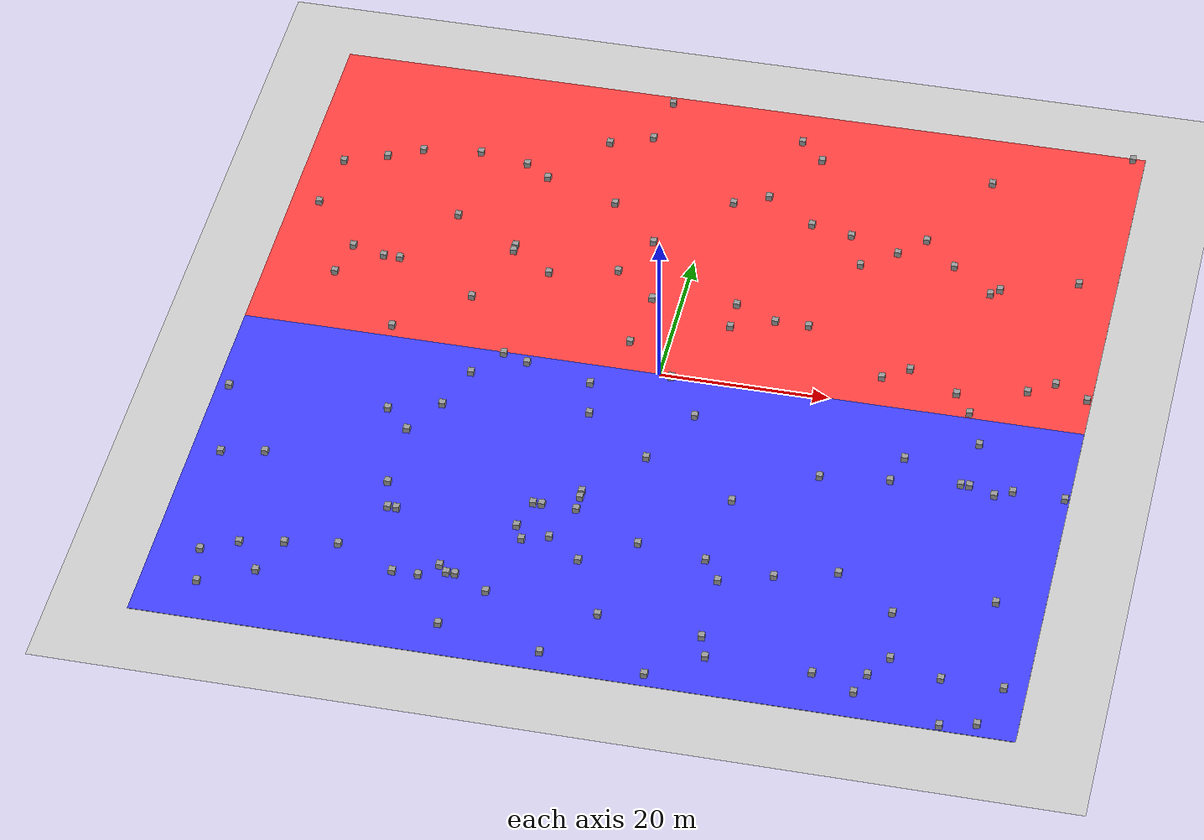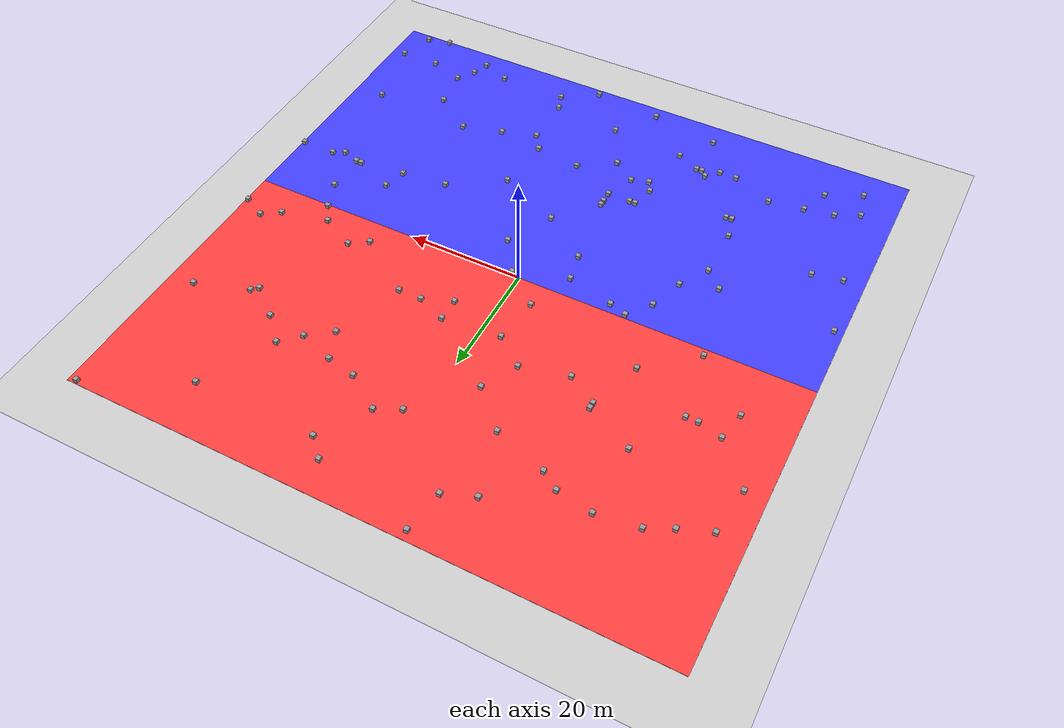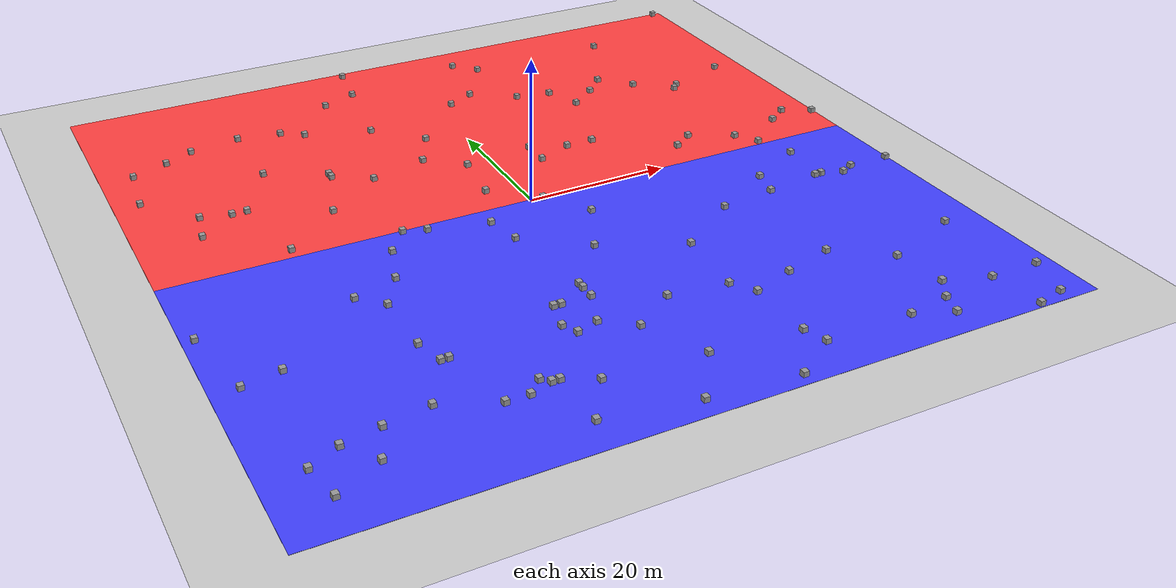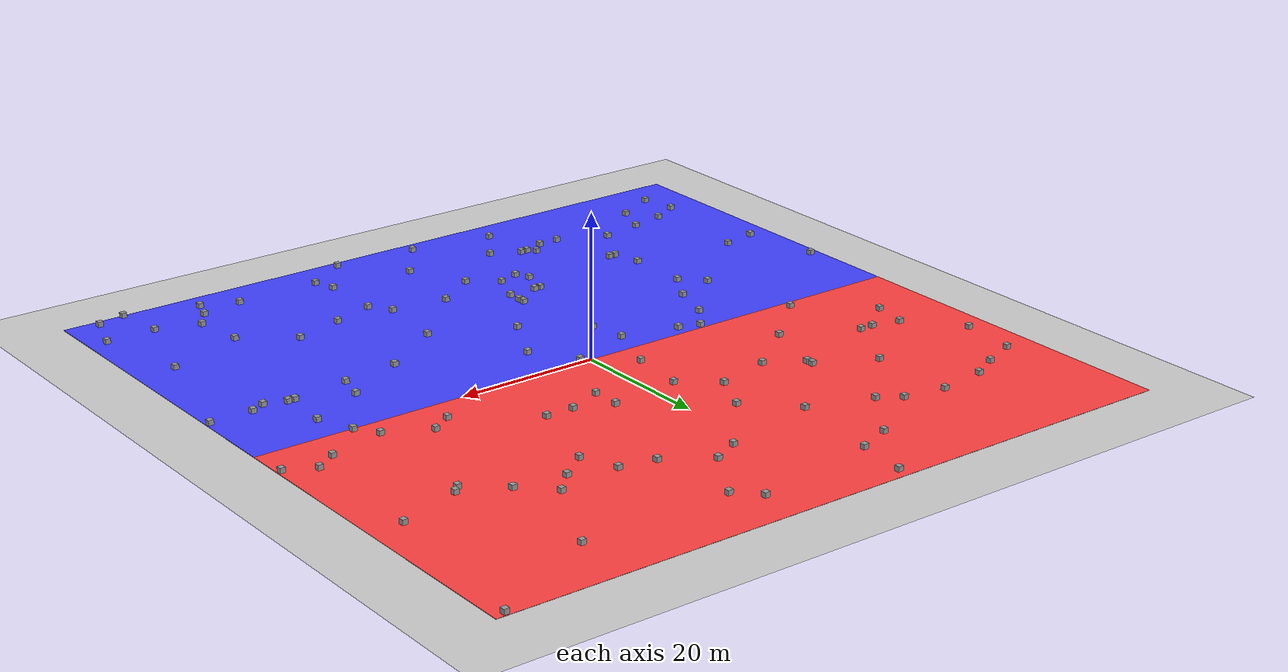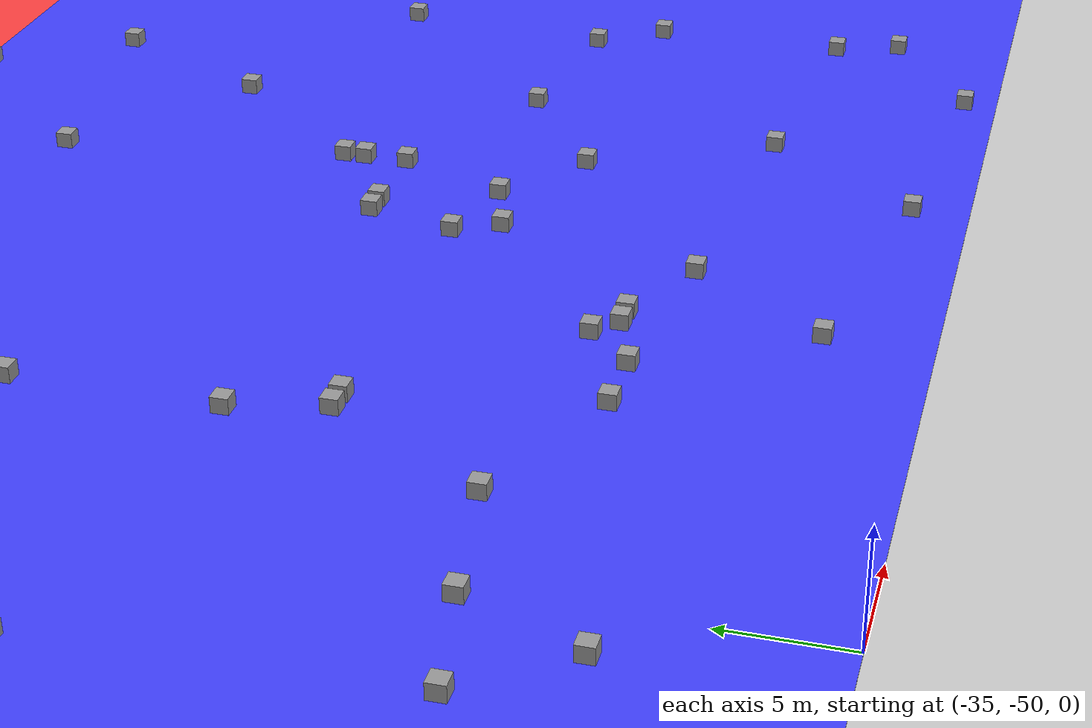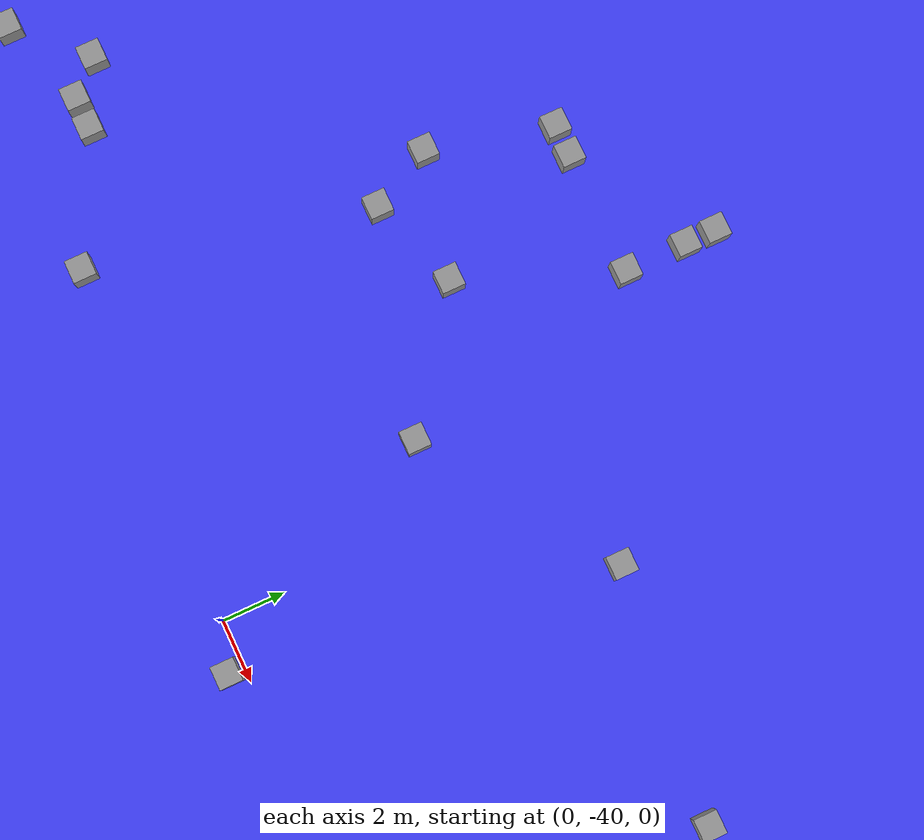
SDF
<sdf version="1.7">
 <world name="default">
  <scene>
   <grid>1</grid>
   <ambient>0.4 0.4 0.4 1</ambient>
   <background>0.7 0.7 0.7 1</background>
   <shadows>1</shadows>
  </scene>
  <light name="sun" type="directional">
   <pose>0 0 10 0 -0 0</pose>
   <diffuse>0.8 0.8 0.8 1</diffuse>
   <specular>0.2 0.2 0.2 1</specular>
   <attenuation>
    <range>1000</range>
    <constant>0.9</constant>
    <linear>0.01</linear>
    <quadratic>0.001</quadratic>
   </attenuation>
   <direction>-0.5 0.1 -0.9</direction>
   <spot><inner_angle>0</inner_angle><outer_angle>0</outer_angle><falloff>0</falloff></spot>
  </light>
  <gravity>0 0 -9.8</gravity>
  <magnetic_field>6e-06 2.3e-05 -4.2e-05</magnetic_field>
  <atmosphere type="adiabatic"/>
  <physics type="ode">
   <max_step_size>0.001</max_step_size>
   <real_time_factor>1</real_time_factor>
   <real_time_update_rate>1000</real_time_update_rate>
  </physics>
  <scene><ambient>0.4 0.4 0.4 1</ambient><background>0.7 0.7 0.7 1</background><shadows>1</shadows></scene>
  <spherical_coordinates>
   <surface_model>EARTH_WGS84</surface_model>
   <latitude_deg>0</latitude_deg>
   <longitude_deg>0</longitude_deg>
   <elevation>0</elevation>
   <heading_deg>0</heading_deg>
  </spherical_coordinates>
  <model name="ground_plane">
   <static>1</static>
   <link name="link">
    <collision name="collision">
     <geometry><plane><normal>0 0 1</normal><size>100 100</size></plane></geometry>
     <surface>
      <contact><collide_bitmask>65535</collide_bitmask></contact>
      <friction><ode><mu>100</mu><mu2>50</mu2></ode></friction>
     </surface>
    </collision>
    <visual name="visual">
     <cast_shadows>0</cast_shadows>
     <geometry><plane><normal>0 0 1</normal><size>100 100</size></plane></geometry>
     <material>
      <script><uri>file://media/materials/scripts/gazebo.material</uri><name>Gazebo/Grey</name></script>
     </material>
    </visual>
   </link>
   <pose>0.004438 -0.003997 0 0 -0 0</pose>
  </model>
  <model name="blue_side">
   <static>1</static>
   <link name="link">
    <visual name="grass">
     <pose>0 -25 0.02 0 -0 0</pose>
     <cast_shadows>0</cast_shadows>
     <geometry><plane><normal>0 0 1</normal><size>100 50</size></plane></geometry>
     <material>
      <ambient>0.25 0.25 1 1</ambient>
      <diffuse>0.25 0.25 1 1</diffuse>
      <specular>0 0 0 0</specular>
      <emissive>0.1 0.1 0.75 1</emissive>
     </material>
    </visual>
   </link>
  </model>
  <model name="blue_block_1">
   <static>1</static>
   <link name="link">
    <visual name="grass">
     <pose>25 25 0.03 0 -0 0</pose>
     <cast_shadows>0</cast_shadows>
     <geometry><plane><normal>0 0 1</normal><size>10 10</size></plane></geometry>
     <material>
      <ambient>0.25 0.25 1 1</ambient>
      <diffuse>0.25 0.25 1 1</diffuse>
      <specular>0 0 0 0</specular>
      <emissive>0.1 0.1 0.75 1</emissive>
     </material>
    </visual>
   </link>
  </model>
  <model name="blue_block_2">
   <static>1</static>
   <link name="link">
    <visual name="grass">
     <pose>-25 25 0.03 0 -0 0</pose>
     <cast_shadows>0</cast_shadows>
     <geometry><plane><normal>0 0 1</normal><size>10 10</size></plane></geometry>
     <material>
      <ambient>0.25 0.25 1 1</ambient>
      <diffuse>0.25 0.25 1 1</diffuse>
      <specular>0 0 0 0</specular>
      <emissive>0.1 0.1 0.75 1</emissive>
     </material>
    </visual>
   </link>
  </model>
  <model name="blue_block_3">
   <static>1</static>
   <link name="link">
    <visual name="grass">
     <pose>0 30 0.03 0 -0 0</pose>
     <cast_shadows>0</cast_shadows>
     <geometry><plane><normal>0 0 1</normal><size>10 10</size></plane></geometry>
     <material>
      <ambient>0.25 0.25 1 1</ambient>
      <diffuse>0.25 0.25 1 1</diffuse>
      <specular>0 0 0 0</specular>
      <emissive>0.1 0.1 0.75 1</emissive>
     </material>
    </visual>
   </link>
  </model>
  <model name="red_side">
   <static>1</static>
   <link name="link">
    <visual name="grass">
     <pose>0 25 0.02 0 -0 0</pose>
     <cast_shadows>0</cast_shadows>
     <geometry><plane><normal>0 0 1</normal><size>100 50</size></plane></geometry>
     <material>
      <ambient>1 0.25 0.25 1</ambient>
      <diffuse>1 0.25 0.25 1</diffuse>
      <specular>0 0 0 0</specular>
      <emissive>0.75 0.1 0.1 1</emissive>
     </material>
    </visual>
   </link>
  </model>
  <model name="red_block_1">
   <static>1</static>
   <link name="link">
    <visual name="grass">
     <pose>25 -25 0.03 0 -0 0</pose>
     <cast_shadows>0</cast_shadows>
     <geometry><plane><normal>0 0 1</normal><size>10 10</size></plane></geometry>
     <material>
      <ambient>1 0.25 0.25 1</ambient>
      <diffuse>1 0.25 0.25 1</diffuse>
      <specular>0 0 0 0</specular>
      <emissive>0.75 0.1 0.1 1</emissive>
     </material>
    </visual>
   </link>
  </model>
  <model name="red_block_2">
   <static>1</static>
   <link name="link">
    <visual name="grass">
     <pose>-25 -25 0.03 0 -0 0</pose>
     <cast_shadows>0</cast_shadows>
     <geometry><plane><normal>0 0 1</normal><size>10 10</size></plane></geometry>
     <material>
      <ambient>1 0.25 0.25 1</ambient>
      <diffuse>1 0.25 0.25 1</diffuse>
      <specular>0 0 0 0</specular>
      <emissive>0.75 0.1 0.1 1</emissive>
     </material>
    </visual>
   </link>
  </model>
  <model name="red_block_3">
   <static>1</static>
   <link name="link">
    <visual name="grass">
     <pose>0 -35 0.03 0 -0 0</pose>
     <cast_shadows>0</cast_shadows>
     <geometry><plane><normal>0 0 1</normal><size>10 10</size></plane></geometry>
     <material>
      <ambient>1 0.25 0.25 1</ambient>
      <diffuse>1 0.25 0.25 1</diffuse>
      <specular>0 0 0 0</specular>
      <emissive>0.75 0.1 0.1 1</emissive>
     </material>
    </visual>
   </link>
  </model>
  <model name="unit_box_0">
   <pose>26.5 -28.5 0.375 0 -0 0</pose>
   <link name="link">
    <inertial>
     <mass>1</mass>
     <inertia>
      <ixx>0.166667</ixx>
      <ixy>0</ixy>
      <ixz>0</ixz>
      <iyy>0.166667</iyy>
      <iyz>0</iyz>
      <izz>0.166667</izz>
     </inertia>
    </inertial>
    <collision name="collision"><geometry><box><size>0.75 0.75 0.75</size></box></geometry></collision>
    <visual name="visual">
     <geometry><box><size>0.75 0.75 0.75</size></box></geometry>
     <material>
      <script><name>Gazebo/Grey</name><uri>file://media/materials/scripts/gazebo.material</uri></script>
     </material>
    </visual>
   </link>
  </model>
  <model name="unit_box_1">
   <pose>35.5 21.5 0.375 0 -0 0</pose>
   <link name="link">
    <inertial>
     <mass>1</mass>
     <inertia>
      <ixx>0.166667</ixx>
      <ixy>0</ixy>
      <ixz>0</ixz>
      <iyy>0.166667</iyy>
      <iyz>0</iyz>
      <izz>0.166667</izz>
     </inertia>
    </inertial>
    <collision name="collision"><geometry><box><size>0.75 0.75 0.75</size></box></geometry></collision>
    <visual name="visual">
     <geometry><box><size>0.75 0.75 0.75</size></box></geometry>
     <material>
      <script><name>Gazebo/Grey</name><uri>file://media/materials/scripts/gazebo.material</uri></script>
     </material>
    </visual>
   </link>
  </model>
  <model name="unit_box_2">
   <pose>-6.5 -8.49999 0.375 0 -0 0</pose>
   <link name="link">
    <inertial>
     <mass>1</mass>
     <inertia>
      <ixx>0.166667</ixx>
      <ixy>0</ixy>
      <ixz>0</ixz>
      <iyy>0.166667</iyy>
      <iyz>0</iyz>
      <izz>0.166667</izz>
     </inertia>
    </inertial>
    <collision name="collision"><geometry><box><size>0.75 0.75 0.75</size></box></geometry></collision>
    <visual name="visual">
     <geometry><box><size>0.75 0.75 0.75</size></box></geometry>
     <material>
      <script><name>Gazebo/Grey</name><uri>file://media/materials/scripts/gazebo.material</uri></script>
     </material>
    </visual>
   </link>
  </model>
  <model name="unit_box_3">
   <pose>-15.5 -1.49999 0.375 0 -0 0</pose>
   <link name="link">
    <inertial>
     <mass>1</mass>
     <inertia>
      <ixx>0.166667</ixx>
      <ixy>0</ixy>
      <ixz>0</ixz>
      <iyy>0.166667</iyy>
      <iyz>0</iyz>
      <izz>0.166667</izz>
     </inertia>
    </inertial>
    <collision name="collision"><geometry><box><size>0.75 0.75 0.75</size></box></geometry></collision>
    <visual name="visual">
     <geometry><box><size>0.75 0.75 0.75</size></box></geometry>
     <material>
      <script><name>Gazebo/Grey</name><uri>file://media/materials/scripts/gazebo.material</uri></script>
     </material>
    </visual>
   </link>
  </model>
  <model name="unit_box_4">
   <pose>-23.5 33.5 0.375 0 -0 0</pose>
   <link name="link">
    <inertial>
     <mass>1</mass>
     <inertia>
      <ixx>0.166667</ixx>
      <ixy>0</ixy>
      <ixz>0</ixz>
      <iyy>0.166667</iyy>
      <iyz>0</iyz>
      <izz>0.166667</izz>
     </inertia>
    </inertial>
    <collision name="collision"><geometry><box><size>0.75 0.75 0.75</size></box></geometry></collision>
    <visual name="visual">
     <geometry><box><size>0.75 0.75 0.75</size></box></geometry>
     <material>
      <script><name>Gazebo/Grey</name><uri>file://media/materials/scripts/gazebo.material</uri></script>
     </material>
    </visual>
   </link>
  </model>
  <model name="unit_box_5">
   <pose>33.5 -33.5 0.375 0 -0 0</pose>
   <link name="link">
    <inertial>
     <mass>1</mass>
     <inertia>
      <ixx>0.166667</ixx>
      <ixy>0</ixy>
      <ixz>0</ixz>
      <iyy>0.166667</iyy>
      <iyz>0</iyz>
      <izz>0.166667</izz>
     </inertia>
    </inertial>
    <collision name="collision"><geometry><box><size>0.75 0.75 0.75</size></box></geometry></collision>
    <visual name="visual">
     <geometry><box><size>0.75 0.75 0.75</size></box></geometry>
     <material>
      <script><name>Gazebo/Grey</name><uri>file://media/materials/scripts/gazebo.material</uri></script>
     </material>
    </visual>
   </link>
  </model>
  <model name="unit_box_6">
   <pose>1.5 -40.5 0.375 0 -0 0</pose>
   <link name="link">
    <inertial>
     <mass>1</mass>
     <inertia>
      <ixx>0.166667</ixx>
      <ixy>0</ixy>
      <ixz>0</ixz>
      <iyy>0.166667</iyy>
      <iyz>0</iyz>
      <izz>0.166667</izz>
     </inertia>
    </inertial>
    <collision name="collision"><geometry><box><size>0.75 0.75 0.75</size></box></geometry></collision>
    <visual name="visual">
     <geometry><box><size>0.75 0.75 0.75</size></box></geometry>
     <material>
      <script><name>Gazebo/Grey</name><uri>file://media/materials/scripts/gazebo.material</uri></script>
     </material>
    </visual>
   </link>
  </model>
  <model name="unit_box_7">
   <pose>-40.5 14.5 0.375 0 -0 0</pose>
   <link name="link">
    <inertial>
     <mass>1</mass>
     <inertia>
      <ixx>0.166667</ixx>
      <ixy>0</ixy>
      <ixz>0</ixz>
      <iyy>0.166667</iyy>
      <iyz>0</iyz>
      <izz>0.166667</izz>
     </inertia>
    </inertial>
    <collision name="collision"><geometry><box><size>0.75 0.75 0.75</size></box></geometry></collision>
    <visual name="visual">
     <geometry><box><size>0.75 0.75 0.75</size></box></geometry>
     <material>
      <script><name>Gazebo/Grey</name><uri>file://media/materials/scripts/gazebo.material</uri></script>
     </material>
    </visual>
   </link>
  </model>
  <model name="unit_box">
   <pose>36.5 0.499997 0.375 0 -0 0</pose>
   <link name="link">
    <inertial>
     <mass>1</mass>
     <inertia>
      <ixx>0.166667</ixx>
      <ixy>0</ixy>
      <ixz>0</ixz>
      <iyy>0.166667</iyy>
      <iyz>0</iyz>
      <izz>0.166667</izz>
     </inertia>
    </inertial>
    <collision name="collision"><geometry><box><size>0.75 0.75 0.75</size></box></geometry></collision>
    <visual name="visual">
     <geometry><box><size>0.75 0.75 0.75</size></box></geometry>
     <material>
      <script><name>Gazebo/Grey</name><uri>file://media/materials/scripts/gazebo.material</uri></script>
     </material>
    </visual>
   </link>
  </model>
  <model name="unit_box_8">
   <pose>15.5 11.5 0.375 0 -0 0</pose>
   <link name="link">
    <inertial>
     <mass>1</mass>
     <inertia>
      <ixx>0.166667</ixx>
      <ixy>0</ixy>
      <ixz>0</ixz>
      <iyy>0.166667</iyy>
      <iyz>0</iyz>
      <izz>0.166667</izz>
     </inertia>
    </inertial>
    <collision name="collision"><geometry><box><size>0.75 0.75 0.75</size></box></geometry></collision>
    <visual name="visual">
     <geometry><box><size>0.75 0.75 0.75</size></box></geometry>
     <material>
      <script><name>Gazebo/Grey</name><uri>file://media/materials/scripts/gazebo.material</uri></script>
     </material>
    </visual>
   </link>
  </model>
  <model name="unit_box_9">
   <pose>-8.5 16.5 0.375 0 -0 0</pose>
   <link name="link">
    <inertial>
     <mass>1</mass>
     <inertia>
      <ixx>0.166667</ixx>
      <ixy>0</ixy>
      <ixz>0</ixz>
      <iyy>0.166667</iyy>
      <iyz>0</iyz>
      <izz>0.166667</izz>
     </inertia>
    </inertial>
    <collision name="collision"><geometry><box><size>0.75 0.75 0.75</size></box></geometry></collision>
    <visual name="visual">
     <geometry><box><size>0.75 0.75 0.75</size></box></geometry>
     <material>
      <script><name>Gazebo/Grey</name><uri>file://media/materials/scripts/gazebo.material</uri></script>
     </material>
    </visual>
   </link>
  </model>
  <model name="unit_box_10">
   <pose>-29.5 -12.5 0.375 0 -0 0</pose>
   <link name="link">
    <inertial>
     <mass>1</mass>
     <inertia>
      <ixx>0.166667</ixx>
      <ixy>0</ixy>
      <ixz>0</ixz>
      <iyy>0.166667</iyy>
      <iyz>0</iyz>
      <izz>0.166667</izz>
     </inertia>
    </inertial>
    <collision name="collision"><geometry><box><size>0.75 0.75 0.75</size></box></geometry></collision>
    <visual name="visual">
     <geometry><box><size>0.75 0.75 0.75</size></box></geometry>
     <material>
      <script><name>Gazebo/Grey</name><uri>file://media/materials/scripts/gazebo.material</uri></script>
     </material>
    </visual>
   </link>
  </model>
  <model name="unit_box_11">
   <pose>21.5 -13.5 0.375 0 -0 0</pose>
   <link name="link">
    <inertial>
     <mass>1</mass>
     <inertia>
      <ixx>0.166667</ixx>
      <ixy>0</ixy>
      <ixz>0</ixz>
      <iyy>0.166667</iyy>
      <iyz>0</iyz>
      <izz>0.166667</izz>
     </inertia>
    </inertial>
    <collision name="collision"><geometry><box><size>0.75 0.75 0.75</size></box></geometry></collision>
    <visual name="visual">
     <geometry><box><size>0.75 0.75 0.75</size></box></geometry>
     <material>
      <script><name>Gazebo/Grey</name><uri>file://media/materials/scripts/gazebo.material</uri></script>
     </material>
    </visual>
   </link>
  </model>
  <model name="unit_box_12">
   <pose>-8.5 -24.5 0.375 0 -0 0</pose>
   <link name="link">
    <inertial>
     <mass>1</mass>
     <inertia>
      <ixx>0.166667</ixx>
      <ixy>0</ixy>
      <ixz>0</ixz>
      <iyy>0.166667</iyy>
      <iyz>0</iyz>
      <izz>0.166667</izz>
     </inertia>
    </inertial>
    <collision name="collision"><geometry><box><size>0.75 0.75 0.75</size></box></geometry></collision>
    <visual name="visual">
     <geometry><box><size>0.75 0.75 0.75</size></box></geometry>
     <material>
      <script><name>Gazebo/Grey</name><uri>file://media/materials/scripts/gazebo.material</uri></script>
     </material>
    </visual>
   </link>
  </model>
  <model name="unit_box_13">
   <pose>-25.5 -28.5 0.375 0 -0 0</pose>
   <link name="link">
    <inertial>
     <mass>1</mass>
     <inertia>
      <ixx>0.166667</ixx>
      <ixy>0</ixy>
      <ixz>0</ixz>
      <iyy>0.166667</iyy>
      <iyz>0</iyz>
      <izz>0.166667</izz>
     </inertia>
    </inertial>
    <collision name="collision"><geometry><box><size>0.75 0.75 0.75</size></box></geometry></collision>
    <visual name="visual">
     <geometry><box><size>0.75 0.75 0.75</size></box></geometry>
     <material>
      <script><name>Gazebo/Grey</name><uri>file://media/materials/scripts/gazebo.material</uri></script>
     </material>
    </visual>
   </link>
  </model>
  <model name="unit_box_14">
   <pose>-2.5 -32.5 0.375 0 -0 0</pose>
   <link name="link">
    <inertial>
     <mass>1</mass>
     <inertia>
      <ixx>0.166667</ixx>
      <ixy>0</ixy>
      <ixz>0</ixz>
      <iyy>0.166667</iyy>
      <iyz>0</iyz>
      <izz>0.166667</izz>
     </inertia>
    </inertial>
    <collision name="collision"><geometry><box><size>0.75 0.75 0.75</size></box></geometry></collision>
    <visual name="visual">
     <geometry><box><size>0.75 0.75 0.75</size></box></geometry>
     <material>
      <script><name>Gazebo/Grey</name><uri>file://media/materials/scripts/gazebo.material</uri></script>
     </material>
    </visual>
   </link>
  </model>
  <model name="unit_box_15">
   <pose>2.5 31.5 0.375 0 -0 0</pose>
   <link name="link">
    <inertial>
     <mass>1</mass>
     <inertia>
      <ixx>0.166667</ixx>
      <ixy>0</ixy>
      <ixz>0</ixz>
      <iyy>0.166667</iyy>
      <iyz>0</iyz>
      <izz>0.166667</izz>
     </inertia>
    </inertial>
    <collision name="collision"><geometry><box><size>0.75 0.75 0.75</size></box></geometry></collision>
    <visual name="visual">
     <geometry><box><size>0.75 0.75 0.75</size></box></geometry>
     <material>
      <script><name>Gazebo/Grey</name><uri>file://media/materials/scripts/gazebo.material</uri></script>
     </material>
    </visual>
   </link>
  </model>
  <model name="unit_box_16">
   <pose>23.5 26.5 0.375 0 -0 0</pose>
   <link name="link">
    <inertial>
     <mass>1</mass>
     <inertia>
      <ixx>0.166667</ixx>
      <ixy>0</ixy>
      <ixz>0</ixz>
      <iyy>0.166667</iyy>
      <iyz>0</iyz>
      <izz>0.166667</izz>
     </inertia>
    </inertial>
    <collision name="collision"><geometry><box><size>0.75 0.75 0.75</size></box></geometry></collision>
    <visual name="visual">
     <geometry><box><size>0.75 0.75 0.75</size></box></geometry>
     <material>
      <script><name>Gazebo/Grey</name><uri>file://media/materials/scripts/gazebo.material</uri></script>
     </material>
    </visual>
   </link>
  </model>
  <model name="unit_box_17">
   <pose>32.5 41.5 0.375 0 -0 0</pose>
   <link name="link">
    <inertial>
     <mass>1</mass>
     <inertia>
      <ixx>0.166667</ixx>
      <ixy>0</ixy>
      <ixz>0</ixz>
      <iyy>0.166667</iyy>
      <iyz>0</iyz>
      <izz>0.166667</izz>
     </inertia>
    </inertial>
    <collision name="collision"><geometry><box><size>0.75 0.75 0.75</size></box></geometry></collision>
    <visual name="visual">
     <geometry><box><size>0.75 0.75 0.75</size></box></geometry>
     <material>
      <script><name>Gazebo/Grey</name><uri>file://media/materials/scripts/gazebo.material</uri></script>
     </material>
    </visual>
   </link>
  </model>
  <model name="unit_box_18">
   <pose>11.5 41.5 0.375 0 -0 0</pose>
   <link name="link">
    <inertial>
     <mass>1</mass>
     <inertia>
      <ixx>0.166667</ixx>
      <ixy>0</ixy>
      <ixz>0</ixz>
      <iyy>0.166667</iyy>
      <iyz>0</iyz>
      <izz>0.166667</izz>
     </inertia>
    </inertial>
    <collision name="collision"><geometry><box><size>0.75 0.75 0.75</size></box></geometry></collision>
    <visual name="visual">
     <geometry><box><size>0.75 0.75 0.75</size></box></geometry>
     <material>
      <script><name>Gazebo/Grey</name><uri>file://media/materials/scripts/gazebo.material</uri></script>
     </material>
    </visual>
   </link>
  </model>
  <model name="unit_box_19">
   <pose>-14.5 39.5 0.375 0 -0 0</pose>
   <link name="link">
    <inertial>
     <mass>1</mass>
     <inertia>
      <ixx>0.166667</ixx>
      <ixy>0</ixy>
      <ixz>0</ixz>
      <iyy>0.166667</iyy>
      <iyz>0</iyz>
      <izz>0.166667</izz>
     </inertia>
    </inertial>
    <collision name="collision"><geometry><box><size>0.75 0.75 0.75</size></box></geometry></collision>
    <visual name="visual">
     <geometry><box><size>0.75 0.75 0.75</size></box></geometry>
     <material>
      <script><name>Gazebo/Grey</name><uri>file://media/materials/scripts/gazebo.material</uri></script>
     </material>
    </visual>
   </link>
  </model>
  <model name="unit_box__0">
   <link name="my_box">
    <inertial>
     <pose>0 0 1 0 -0 0</pose>
     <mass>1</mass>
     <inertia><ixx>1</ixx><ixy>0</ixy><ixz>0</ixz><iyy>100</iyy><iyz>0</iyz><izz>1</izz></inertia>
    </inertial>
    <collision name="my_box_collision">
     <pose>0 0 1 0 -0 0</pose>
     <geometry><box><size>0.75 0.75 0.75</size></box></geometry>
    </collision>
    <visual name="my_box_visual">
     <pose>0 0 1 0 -0 0</pose>
     <geometry><box><size>0.75 0.75 0.75</size></box></geometry>
     <material>
      <script><name>Gazebo/Grey</name><uri>file://media/materials/scripts/gazebo.material</uri></script>
     </material>
    </visual>
   </link>
   <pose>-4.50038 -22.5 -0.624759 1e-06 0.00064 -1.4e-05</pose>
  </model>
  <model name="unit_box__1">
   <link name="my_box">
    <inertial>
     <pose>0 0 1 0 -0 0</pose>
     <mass>1</mass>
     <inertia><ixx>1</ixx><ixy>0</ixy><ixz>0</ixz><iyy>100</iyy><iyz>0</iyz><izz>1</izz></inertia>
    </inertial>
    <collision name="my_box_collision">
     <pose>0 0 1 0 -0 0</pose>
     <geometry><box><size>0.75 0.75 0.75</size></box></geometry>
    </collision>
    <visual name="my_box_visual">
     <pose>0 0 1 0 -0 0</pose>
     <geometry><box><size>0.75 0.75 0.75</size></box></geometry>
     <material>
      <script><name>Gazebo/Grey</name><uri>file://media/materials/scripts/gazebo.material</uri></script>
     </material>
    </visual>
   </link>
   <pose>45.5001 -48.5 -0.624939 2e-06 -0.000164 -1.8e-05</pose>
  </model>
  <model name="unit_box__2">
   <link name="my_box">
    <inertial>
     <pose>0 0 1 0 -0 0</pose>
     <mass>1</mass>
     <inertia><ixx>1</ixx><ixy>0</ixy><ixz>0</ixz><iyy>100</iyy><iyz>0</iyz><izz>1</izz></inertia>
    </inertial>
    <collision name="my_box_collision">
     <pose>0 0 1 0 -0 0</pose>
     <geometry><box><size>0.75 0.75 0.75</size></box></geometry>
    </collision>
    <visual name="my_box_visual">
     <pose>0 0 1 0 -0 0</pose>
     <geometry><box><size>0.75 0.75 0.75</size></box></geometry>
     <material>
      <script><name>Gazebo/Grey</name><uri>file://media/materials/scripts/gazebo.material</uri></script>
     </material>
    </visual>
   </link>
   <pose>-15.4996 -37.5 -0.62475 1e-06 -0.000666 -3e-05</pose>
  </model>
  <model name="unit_box__3">
   <link name="my_box">
    <inertial>
     <pose>0 0 1 0 -0 0</pose>
     <mass>1</mass>
     <inertia><ixx>1</ixx><ixy>0</ixy><ixz>0</ixz><iyy>100</iyy><iyz>0</iyz><izz>1</izz></inertia>
    </inertial>
    <collision name="my_box_collision">
     <pose>0 0 1 0 -0 0</pose>
     <geometry><box><size>0.75 0.75 0.75</size></box></geometry>
    </collision>
    <visual name="my_box_visual">
     <pose>0 0 1 0 -0 0</pose>
     <geometry><box><size>0.75 0.75 0.75</size></box></geometry>
     <material>
      <script><name>Gazebo/Grey</name><uri>file://media/materials/scripts/gazebo.material</uri></script>
     </material>
    </visual>
   </link>
   <pose>12.5 -19.5 -0.624972 -1e-06 7.4e-05 -2.7e-05</pose>
  </model>
  <model name="unit_box__4">
   <link name="my_box">
    <inertial>
     <pose>0 0 1 0 -0 0</pose>
     <mass>1</mass>
     <inertia><ixx>1</ixx><ixy>0</ixy><ixz>0</ixz><iyy>100</iyy><iyz>0</iyz><izz>1</izz></inertia>
    </inertial>
    <collision name="my_box_collision">
     <pose>0 0 1 0 -0 0</pose>
     <geometry><box><size>0.75 0.75 0.75</size></box></geometry>
    </collision>
    <visual name="my_box_visual">
     <pose>0 0 1 0 -0 0</pose>
     <geometry><box><size>0.75 0.75 0.75</size></box></geometry>
     <material>
      <script><name>Gazebo/Grey</name><uri>file://media/materials/scripts/gazebo.material</uri></script>
     </material>
    </visual>
   </link>
   <pose>45.4996 7.5 -0.624747 -1e-06 0.000674 -1.6e-05</pose>
  </model>
  <model name="unit_box__5">
   <link name="my_box">
    <inertial>
     <pose>0 0 1 0 -0 0</pose>
     <mass>1</mass>
     <inertia><ixx>1</ixx><ixy>0</ixy><ixz>0</ixz><iyy>100</iyy><iyz>0</iyz><izz>1</izz></inertia>
    </inertial>
    <collision name="my_box_collision">
     <pose>0 0 1 0 -0 0</pose>
     <geometry><box><size>0.75 0.75 0.75</size></box></geometry>
    </collision>
    <visual name="my_box_visual">
     <pose>0 0 1 0 -0 0</pose>
     <geometry><box><size>0.75 0.75 0.75</size></box></geometry>
     <material>
      <script><name>Gazebo/Grey</name><uri>file://media/materials/scripts/gazebo.material</uri></script>
     </material>
    </visual>
   </link>
   <pose>12.4999 29.5 -0.624959 1e-06 0.000108 -1.4e-05</pose>
  </model>
  <model name="unit_box__6">
   <link name="my_box">
    <inertial>
     <pose>0 0 1 0 -0 0</pose>
     <mass>1</mass>
     <inertia><ixx>1</ixx><ixy>0</ixy><ixz>0</ixz><iyy>100</iyy><iyz>0</iyz><izz>1</izz></inertia>
    </inertial>
    <collision name="my_box_collision">
     <pose>0 0 1 0 -0 0</pose>
     <geometry><box><size>0.75 0.75 0.75</size></box></geometry>
    </collision>
    <visual name="my_box_visual">
     <pose>0 0 1 0 -0 0</pose>
     <geometry><box><size>0.75 0.75 0.75</size></box></geometry>
     <material>
      <script><name>Gazebo/Grey</name><uri>file://media/materials/scripts/gazebo.material</uri></script>
     </material>
    </visual>
   </link>
   <pose>-4.49955 -21.5 -0.624742 1e-06 -0.000686 -9e-06</pose>
  </model>
  <model name="unit_box__7">
   <link name="my_box">
    <inertial>
     <pose>0 0 1 0 -0 0</pose>
     <mass>1</mass>
     <inertia><ixx>1</ixx><ixy>0</ixy><ixz>0</ixz><iyy>100</iyy><iyz>0</iyz><izz>1</izz></inertia>
    </inertial>
    <collision name="my_box_collision">
     <pose>0 0 1 0 -0 0</pose>
     <geometry><box><size>0.75 0.75 0.75</size></box></geometry>
    </collision>
    <visual name="my_box_visual">
     <pose>0 0 1 0 -0 0</pose>
     <geometry><box><size>0.75 0.75 0.75</size></box></geometry>
     <material>
      <script><name>Gazebo/Grey</name><uri>file://media/materials/scripts/gazebo.material</uri></script>
     </material>
    </visual>
   </link>
   <pose>-37.5 -41.5 -0.624984 -2e-06 4.4e-05 -1.8e-05</pose>
  </model>
  <model name="unit_box__8">
   <link name="my_box">
    <inertial>
     <pose>0 0 1 0 -0 0</pose>
     <mass>1</mass>
     <inertia><ixx>1</ixx><ixy>0</ixy><ixz>0</ixz><iyy>100</iyy><iyz>0</iyz><izz>1</izz></inertia>
    </inertial>
    <collision name="my_box_collision">
     <pose>0 0 1 0 -0 0</pose>
     <geometry><box><size>0.75 0.75 0.75</size></box></geometry>
    </collision>
    <visual name="my_box_visual">
     <pose>0 0 1 0 -0 0</pose>
     <geometry><box><size>0.75 0.75 0.75</size></box></geometry>
     <material>
      <script><name>Gazebo/Grey</name><uri>file://media/materials/scripts/gazebo.material</uri></script>
     </material>
    </visual>
   </link>
   <pose>49.4996 5.5 -0.624729 -1e-06 0.00072 -1.2e-05</pose>
  </model>
  <model name="unit_box__10">
   <link name="my_box">
    <inertial>
     <pose>0 0 1 0 -0 0</pose>
     <mass>1</mass>
     <inertia><ixx>1</ixx><ixy>0</ixy><ixz>0</ixz><iyy>100</iyy><iyz>0</iyz><izz>1</izz></inertia>
    </inertial>
    <collision name="my_box_collision">
     <pose>0 0 1 0 -0 0</pose>
     <geometry><box><size>0.75 0.75 0.75</size></box></geometry>
    </collision>
    <visual name="my_box_visual">
     <pose>0 0 1 0 -0 0</pose>
     <geometry><box><size>0.75 0.75 0.75</size></box></geometry>
     <material>
      <script><name>Gazebo/Grey</name><uri>file://media/materials/scripts/gazebo.material</uri></script>
     </material>
    </visual>
   </link>
   <pose>11.5 -29.5 -0.624991 -2e-06 2.7e-05 3e-06</pose>
  </model>
  <model name="unit_box__11">
   <link name="my_box">
    <inertial>
     <pose>0 0 1 0 -0 0</pose>
     <mass>1</mass>
     <inertia><ixx>1</ixx><ixy>0</ixy><ixz>0</ixz><iyy>100</iyy><iyz>0</iyz><izz>1</izz></inertia>
    </inertial>
    <collision name="my_box_collision">
     <pose>0 0 1 0 -0 0</pose>
     <geometry><box><size>0.75 0.75 0.75</size></box></geometry>
    </collision>
    <visual name="my_box_visual">
     <pose>0 0 1 0 -0 0</pose>
     <geometry><box><size>0.75 0.75 0.75</size></box></geometry>
     <material>
      <script><name>Gazebo/Grey</name><uri>file://media/materials/scripts/gazebo.material</uri></script>
     </material>
    </visual>
   </link>
   <pose>-16.4995 -37.5 -0.624734 -2e-06 -0.000711 -3e-06</pose>
  </model>
  <model name="unit_box__12">
   <link name="my_box">
    <inertial>
     <pose>0 0 1 0 -0 0</pose>
     <mass>1</mass>
     <inertia><ixx>1</ixx><ixy>0</ixy><ixz>0</ixz><iyy>100</iyy><iyz>0</iyz><izz>1</izz></inertia>
    </inertial>
    <collision name="my_box_collision">
     <pose>0 0 1 0 -0 0</pose>
     <geometry><box><size>0.75 0.75 0.75</size></box></geometry>
    </collision>
    <visual name="my_box_visual">
     <pose>0 0 1 0 -0 0</pose>
     <geometry><box><size>0.75 0.75 0.75</size></box></geometry>
     <material>
      <script><name>Gazebo/Grey</name><uri>file://media/materials/scripts/gazebo.material</uri></script>
     </material>
    </visual>
   </link>
   <pose>45.5001 25.5 -0.624996 -1e-06 -1.1e-05 2e-05</pose>
  </model>
  <model name="unit_box__13">
   <link name="my_box">
    <inertial>
     <pose>0 0 1 0 -0 0</pose>
     <mass>1</mass>
     <inertia><ixx>1</ixx><ixy>0</ixy><ixz>0</ixz><iyy>100</iyy><iyz>0</iyz><izz>1</izz></inertia>
    </inertial>
    <collision name="my_box_collision">
     <pose>0 0 1 0 -0 0</pose>
     <geometry><box><size>0.75 0.75 0.75</size></box></geometry>
    </collision>
    <visual name="my_box_visual">
     <pose>0 0 1 0 -0 0</pose>
     <geometry><box><size>0.75 0.75 0.75</size></box></geometry>
     <material>
      <script><name>Gazebo/Grey</name><uri>file://media/materials/scripts/gazebo.material</uri></script>
     </material>
    </visual>
   </link>
   <pose>17.4996 28.5 -0.624725 -1e-06 0.000732 -4e-06</pose>
  </model>
  <model name="unit_box__14">
   <link name="my_box">
    <inertial>
     <pose>0 0 1 0 -0 0</pose>
     <mass>1</mass>
     <inertia><ixx>1</ixx><ixy>0</ixy><ixz>0</ixz><iyy>100</iyy><iyz>0</iyz><izz>1</izz></inertia>
    </inertial>
    <collision name="my_box_collision">
     <pose>0 0 1 0 -0 0</pose>
     <geometry><box><size>0.75 0.75 0.75</size></box></geometry>
    </collision>
    <visual name="my_box_visual">
     <pose>0 0 1 0 -0 0</pose>
     <geometry><box><size>0.75 0.75 0.75</size></box></geometry>
     <material>
      <script><name>Gazebo/Grey</name><uri>file://media/materials/scripts/gazebo.material</uri></script>
     </material>
    </visual>
   </link>
   <pose>6.50002 33.5 -0.624996 -1e-06 -1e-05 -9e-06</pose>
  </model>
  <model name="unit_box__15">
   <link name="my_box">
    <inertial>
     <pose>0 0 1 0 -0 0</pose>
     <mass>1</mass>
     <inertia><ixx>1</ixx><ixy>0</ixy><ixz>0</ixz><iyy>100</iyy><iyz>0</iyz><izz>1</izz></inertia>
    </inertial>
    <collision name="my_box_collision">
     <pose>0 0 1 0 -0 0</pose>
     <geometry><box><size>0.75 0.75 0.75</size></box></geometry>
    </collision>
    <visual name="my_box_visual">
     <pose>0 0 1 0 -0 0</pose>
     <geometry><box><size>0.75 0.75 0.75</size></box></geometry>
     <material>
      <script><name>Gazebo/Grey</name><uri>file://media/materials/scripts/gazebo.material</uri></script>
     </material>
    </visual>
   </link>
   <pose>26.5005 -44.5 -0.624726 -2e-06 -0.000733 2e-06</pose>
  </model>
  <model name="unit_box__16">
   <link name="my_box">
    <inertial>
     <pose>0 0 1 0 -0 0</pose>
     <mass>1</mass>
     <inertia><ixx>1</ixx><ixy>0</ixy><ixz>0</ixz><iyy>100</iyy><iyz>0</iyz><izz>1</izz></inertia>
    </inertial>
    <collision name="my_box_collision">
     <pose>0 0 1 0 -0 0</pose>
     <geometry><box><size>0.75 0.75 0.75</size></box></geometry>
    </collision>
    <visual name="my_box_visual">
     <pose>0 0 1 0 -0 0</pose>
     <geometry><box><size>0.75 0.75 0.75</size></box></geometry>
     <material>
      <script><name>Gazebo/Grey</name><uri>file://media/materials/scripts/gazebo.material</uri></script>
     </material>
    </visual>
   </link>
   <pose>38.5 -4.49999 -0.624991 -2e-06 2.6e-05 -1.1e-05</pose>
  </model>
  <model name="unit_box__17">
   <link name="my_box">
    <inertial>
     <pose>0 0 1 0 -0 0</pose>
     <mass>1</mass>
     <inertia><ixx>1</ixx><ixy>0</ixy><ixz>0</ixz><iyy>100</iyy><iyz>0</iyz><izz>1</izz></inertia>
    </inertial>
    <collision name="my_box_collision">
     <pose>0 0 1 0 -0 0</pose>
     <geometry><box><size>0.75 0.75 0.75</size></box></geometry>
    </collision>
    <visual name="my_box_visual">
     <pose>0 0 1 0 -0 0</pose>
     <geometry><box><size>0.75 0.75 0.75</size></box></geometry>
     <material>
      <script><name>Gazebo/Grey</name><uri>file://media/materials/scripts/gazebo.material</uri></script>
     </material>
    </visual>
   </link>
   <pose>36.4996 22.5 -0.624728 2e-06 0.000728 2e-06</pose>
  </model>
  <model name="unit_box__18">
   <link name="my_box">
    <inertial>
     <pose>0 0 1 0 -0 0</pose>
     <mass>1</mass>
     <inertia><ixx>1</ixx><ixy>0</ixy><ixz>0</ixz><iyy>100</iyy><iyz>0</iyz><izz>1</izz></inertia>
    </inertial>
    <collision name="my_box_collision">
     <pose>0 0 1 0 -0 0</pose>
     <geometry><box><size>0.75 0.75 0.75</size></box></geometry>
    </collision>
    <visual name="my_box_visual">
     <pose>0 0 1 0 -0 0</pose>
     <geometry><box><size>0.75 0.75 0.75</size></box></geometry>
     <material>
      <script><name>Gazebo/Grey</name><uri>file://media/materials/scripts/gazebo.material</uri></script>
     </material>
    </visual>
   </link>
   <pose>-43.5 -44.5 -0.624975 2e-06 7e-05 -2.3e-05</pose>
  </model>
  <model name="unit_box__19">
   <link name="my_box">
    <inertial>
     <pose>0 0 1 0 -0 0</pose>
     <mass>1</mass>
     <inertia><ixx>1</ixx><ixy>0</ixy><ixz>0</ixz><iyy>100</iyy><iyz>0</iyz><izz>1</izz></inertia>
    </inertial>
    <collision name="my_box_collision">
     <pose>0 0 1 0 -0 0</pose>
     <geometry><box><size>0.75 0.75 0.75</size></box></geometry>
    </collision>
    <visual name="my_box_visual">
     <pose>0 0 1 0 -0 0</pose>
     <geometry><box><size>0.75 0.75 0.75</size></box></geometry>
     <material>
      <script><name>Gazebo/Grey</name><uri>file://media/materials/scripts/gazebo.material</uri></script>
     </material>
    </visual>
   </link>
   <pose>1.50047 -14.5 -0.62473 2e-06 -0.000721 2e-06</pose>
  </model>
  <model name="unit_box__20">
   <link name="my_box">
    <inertial>
     <pose>0 0 1 0 -0 0</pose>
     <mass>1</mass>
     <inertia><ixx>1</ixx><ixy>0</ixy><ixz>0</ixz><iyy>100</iyy><iyz>0</iyz><izz>1</izz></inertia>
    </inertial>
    <collision name="my_box_collision">
     <pose>0 0 1 0 -0 0</pose>
     <geometry><box><size>0.75 0.75 0.75</size></box></geometry>
    </collision>
    <visual name="my_box_visual">
     <pose>0 0 1 0 -0 0</pose>
     <geometry><box><size>0.75 0.75 0.75</size></box></geometry>
     <material>
      <script><name>Gazebo/Grey</name><uri>file://media/materials/scripts/gazebo.material</uri></script>
     </material>
    </visual>
   </link>
   <pose>-19.4999 -38.5 -0.624975 -8e-06 -5.8e-05 -4e-06</pose>
  </model>
  <model name="unit_box__21">
   <link name="my_box">
    <inertial>
     <pose>0 0 1 0 -0 0</pose>
     <mass>1</mass>
     <inertia><ixx>1</ixx><ixy>0</ixy><ixz>0</ixz><iyy>100</iyy><iyz>0</iyz><izz>1</izz></inertia>
    </inertial>
    <collision name="my_box_collision">
     <pose>0 0 1 0 -0 0</pose>
     <geometry><box><size>0.75 0.75 0.75</size></box></geometry>
    </collision>
    <visual name="my_box_visual">
     <pose>0 0 1 0 -0 0</pose>
     <geometry><box><size>0.75 0.75 0.75</size></box></geometry>
     <material>
      <script><name>Gazebo/Grey</name><uri>file://media/materials/scripts/gazebo.material</uri></script>
     </material>
    </visual>
   </link>
   <pose>-32.5004 1.5 -0.624726 -1e-06 0.000728 4e-06</pose>
  </model>
  <model name="unit_box__22">
   <link name="my_box">
    <inertial>
     <pose>0 0 1 0 -0 0</pose>
     <mass>1</mass>
     <inertia><ixx>1</ixx><ixy>0</ixy><ixz>0</ixz><iyy>100</iyy><iyz>0</iyz><izz>1</izz></inertia>
    </inertial>
    <collision name="my_box_collision">
     <pose>0 0 1 0 -0 0</pose>
     <geometry><box><size>0.75 0.75 0.75</size></box></geometry>
    </collision>
    <visual name="my_box_visual">
     <pose>0 0 1 0 -0 0</pose>
     <geometry><box><size>0.75 0.75 0.75</size></box></geometry>
     <material>
      <script><name>Gazebo/Grey</name><uri>file://media/materials/scripts/gazebo.material</uri></script>
     </material>
    </visual>
   </link>
   <pose>5.4999 -6.49999 -0.624937 2e-06 0.00017 1.6e-05</pose>
  </model>
  <model name="unit_box__23">
   <link name="my_box">
    <inertial>
     <pose>0 0 1 0 -0 0</pose>
     <mass>1</mass>
     <inertia><ixx>1</ixx><ixy>0</ixy><ixz>0</ixz><iyy>100</iyy><iyz>0</iyz><izz>1</izz></inertia>
    </inertial>
    <collision name="my_box_collision">
     <pose>0 0 1 0 -0 0</pose>
     <geometry><box><size>0.75 0.75 0.75</size></box></geometry>
    </collision>
    <visual name="my_box_visual">
     <pose>0 0 1 0 -0 0</pose>
     <geometry><box><size>0.75 0.75 0.75</size></box></geometry>
     <material>
      <script><name>Gazebo/Grey</name><uri>file://media/materials/scripts/gazebo.material</uri></script>
     </material>
    </visual>
   </link>
   <pose>13.5005 -41.5 -0.624731 -2e-06 -0.000719 6e-06</pose>
  </model>
  <model name="unit_box__24">
   <link name="my_box">
    <inertial>
     <pose>0 0 1 0 -0 0</pose>
     <mass>1</mass>
     <inertia><ixx>1</ixx><ixy>0</ixy><ixz>0</ixz><iyy>100</iyy><iyz>0</iyz><izz>1</izz></inertia>
    </inertial>
    <collision name="my_box_collision">
     <pose>0 0 1 0 -0 0</pose>
     <geometry><box><size>0.75 0.75 0.75</size></box></geometry>
    </collision>
    <visual name="my_box_visual">
     <pose>0 0 1 0 -0 0</pose>
     <geometry><box><size>0.75 0.75 0.75</size></box></geometry>
     <material>
      <script><name>Gazebo/Grey</name><uri>file://media/materials/scripts/gazebo.material</uri></script>
     </material>
    </visual>
   </link>
   <pose>-26.5001 -15.5 -0.624932 2e-06 0.000184 -1e-06</pose>
  </model>
  <model name="unit_box__25">
   <link name="my_box">
    <inertial>
     <pose>0 0 1 0 -0 0</pose>
     <mass>1</mass>
     <inertia><ixx>1</ixx><ixy>0</ixy><ixz>0</ixz><iyy>100</iyy><iyz>0</iyz><izz>1</izz></inertia>
    </inertial>
    <collision name="my_box_collision">
     <pose>0 0 1 0 -0 0</pose>
     <geometry><box><size>0.75 0.75 0.75</size></box></geometry>
    </collision>
    <visual name="my_box_visual">
     <pose>0 0 1 0 -0 0</pose>
     <geometry><box><size>0.75 0.75 0.75</size></box></geometry>
     <material>
      <script><name>Gazebo/Grey</name><uri>file://media/materials/scripts/gazebo.material</uri></script>
     </material>
    </visual>
   </link>
   <pose>11.4996 11.5 -0.624732 2e-06 0.000716 -9e-06</pose>
  </model>
  <model name="unit_box__26">
   <link name="my_box">
    <inertial>
     <pose>0 0 1 0 -0 0</pose>
     <mass>1</mass>
     <inertia><ixx>1</ixx><ixy>0</ixy><ixz>0</ixz><iyy>100</iyy><iyz>0</iyz><izz>1</izz></inertia>
    </inertial>
    <collision name="my_box_collision">
     <pose>0 0 1 0 -0 0</pose>
     <geometry><box><size>0.75 0.75 0.75</size></box></geometry>
    </collision>
    <visual name="my_box_visual">
     <pose>0 0 1 0 -0 0</pose>
     <geometry><box><size>0.75 0.75 0.75</size></box></geometry>
     <material>
      <script><name>Gazebo/Grey</name><uri>file://media/materials/scripts/gazebo.material</uri></script>
     </material>
    </visual>
   </link>
   <pose>-29.4998 22.5 -0.624858 2e-06 -0.00038 -3e-06</pose>
  </model>
  <model name="unit_box__27">
   <link name="my_box">
    <inertial>
     <pose>0 0 1 0 -0 0</pose>
     <mass>1</mass>
     <inertia><ixx>1</ixx><ixy>0</ixy><ixz>0</ixz><iyy>100</iyy><iyz>0</iyz><izz>1</izz></inertia>
    </inertial>
    <collision name="my_box_collision">
     <pose>0 0 1 0 -0 0</pose>
     <geometry><box><size>0.75 0.75 0.75</size></box></geometry>
    </collision>
    <visual name="my_box_visual">
     <pose>0 0 1 0 -0 0</pose>
     <geometry><box><size>0.75 0.75 0.75</size></box></geometry>
     <material>
      <script><name>Gazebo/Grey</name><uri>file://media/materials/scripts/gazebo.material</uri></script>
     </material>
    </visual>
   </link>
   <pose>34.5005 -40.5 -0.624743 1e-06 -0.000683 3e-06</pose>
  </model>
  <model name="unit_box__28">
   <link name="my_box">
    <inertial>
     <pose>0 0 1 0 -0 0</pose>
     <mass>1</mass>
     <inertia><ixx>1</ixx><ixy>0</ixy><ixz>0</ixz><iyy>100</iyy><iyz>0</iyz><izz>1</izz></inertia>
    </inertial>
    <collision name="my_box_collision">
     <pose>0 0 1 0 -0 0</pose>
     <geometry><box><size>0.75 0.75 0.75</size></box></geometry>
    </collision>
    <visual name="my_box_visual">
     <pose>0 0 1 0 -0 0</pose>
     <geometry><box><size>0.75 0.75 0.75</size></box></geometry>
     <material>
      <script><name>Gazebo/Grey</name><uri>file://media/materials/scripts/gazebo.material</uri></script>
     </material>
    </visual>
   </link>
   <pose>40.5002 -42.5 -0.624924 1e-06 -0.000203 1e-06</pose>
  </model>
  <model name="unit_box__29">
   <link name="my_box">
    <inertial>
     <pose>0 0 1 0 -0 0</pose>
     <mass>1</mass>
     <inertia><ixx>1</ixx><ixy>0</ixy><ixz>0</ixz><iyy>100</iyy><iyz>0</iyz><izz>1</izz></inertia>
    </inertial>
    <collision name="my_box_collision">
     <pose>0 0 1 0 -0 0</pose>
     <geometry><box><size>0.75 0.75 0.75</size></box></geometry>
    </collision>
    <visual name="my_box_visual">
     <pose>0 0 1 0 -0 0</pose>
     <geometry><box><size>0.75 0.75 0.75</size></box></geometry>
     <material>
      <script><name>Gazebo/Grey</name><uri>file://media/materials/scripts/gazebo.material</uri></script>
     </material>
    </visual>
   </link>
   <pose>41.4997 -12.5 -0.624828 2e-06 0.000459 -1e-06</pose>
  </model>
  <model name="unit_box__30">
   <link name="my_box">
    <inertial>
     <pose>0 0 1 0 -0 0</pose>
     <mass>1</mass>
     <inertia><ixx>1</ixx><ixy>0</ixy><ixz>0</ixz><iyy>100</iyy><iyz>0</iyz><izz>1</izz></inertia>
    </inertial>
    <collision name="my_box_collision">
     <pose>0 0 1 0 -0 0</pose>
     <geometry><box><size>0.75 0.75 0.75</size></box></geometry>
    </collision>
    <visual name="my_box_visual">
     <pose>0 0 1 0 -0 0</pose>
     <geometry><box><size>0.75 0.75 0.75</size></box></geometry>
     <material>
      <script><name>Gazebo/Grey</name><uri>file://media/materials/scripts/gazebo.material</uri></script>
     </material>
    </visual>
   </link>
   <pose>-16.5003 14.5 -0.624795 1e-06 0.000546 -1e-06</pose>
  </model>
  <model name="unit_box__31">
   <link name="my_box">
    <inertial>
     <pose>0 0 1 0 -0 0</pose>
     <mass>1</mass>
     <inertia><ixx>1</ixx><ixy>0</ixy><ixz>0</ixz><iyy>100</iyy><iyz>0</iyz><izz>1</izz></inertia>
    </inertial>
    <collision name="my_box_collision">
     <pose>0 0 1 0 -0 0</pose>
     <geometry><box><size>0.75 0.75 0.75</size></box></geometry>
    </collision>
    <visual name="my_box_visual">
     <pose>0 0 1 0 -0 0</pose>
     <geometry><box><size>0.75 0.75 0.75</size></box></geometry>
     <material>
      <script><name>Gazebo/Grey</name><uri>file://media/materials/scripts/gazebo.material</uri></script>
     </material>
    </visual>
   </link>
   <pose>-35.4999 -36.5 -0.624977 1e-06 -6.1e-05 -3e-06</pose>
  </model>
  <model name="unit_box__32">
   <link name="my_box">
    <inertial>
     <pose>0 0 1 0 -0 0</pose>
     <mass>1</mass>
     <inertia><ixx>1</ixx><ixy>0</ixy><ixz>0</ixz><iyy>100</iyy><iyz>0</iyz><izz>1</izz></inertia>
    </inertial>
    <collision name="my_box_collision">
     <pose>0 0 1 0 -0 0</pose>
     <geometry><box><size>0.75 0.75 0.75</size></box></geometry>
    </collision>
    <visual name="my_box_visual">
     <pose>0 0 1 0 -0 0</pose>
     <geometry><box><size>0.75 0.75 0.75</size></box></geometry>
     <material>
      <script><name>Gazebo/Grey</name><uri>file://media/materials/scripts/gazebo.material</uri></script>
     </material>
    </visual>
   </link>
   <pose>-34.4995 13.5 -0.624729 -1e-06 -0.000722 -2.3e-05</pose>
  </model>
  <model name="unit_box__33">
   <link name="my_box">
    <inertial>
     <pose>0 0 1 0 -0 0</pose>
     <mass>1</mass>
     <inertia><ixx>1</ixx><ixy>0</ixy><ixz>0</ixz><iyy>100</iyy><iyz>0</iyz><izz>1</izz></inertia>
    </inertial>
    <collision name="my_box_collision">
     <pose>0 0 1 0 -0 0</pose>
     <geometry><box><size>0.75 0.75 0.75</size></box></geometry>
    </collision>
    <visual name="my_box_visual">
     <pose>0 0 1 0 -0 0</pose>
     <geometry><box><size>0.75 0.75 0.75</size></box></geometry>
     <material>
      <script><name>Gazebo/Grey</name><uri>file://media/materials/scripts/gazebo.material</uri></script>
     </material>
    </visual>
   </link>
   <pose>-21.4997 17.5 -0.624856 1e-06 -0.000382 -1.1e-05</pose>
  </model>
  <model name="unit_box__34">
   <link name="my_box">
    <inertial>
     <pose>0 0 1 0 -0 0</pose>
     <mass>1</mass>
     <inertia><ixx>1</ixx><ixy>0</ixy><ixz>0</ixz><iyy>100</iyy><iyz>0</iyz><izz>1</izz></inertia>
    </inertial>
    <collision name="my_box_collision">
     <pose>0 0 1 0 -0 0</pose>
     <geometry><box><size>0.75 0.75 0.75</size></box></geometry>
    </collision>
    <visual name="my_box_visual">
     <pose>0 0 1 0 -0 0</pose>
     <geometry><box><size>0.75 0.75 0.75</size></box></geometry>
     <material>
      <script><name>Gazebo/Grey</name><uri>file://media/materials/scripts/gazebo.material</uri></script>
     </material>
    </visual>
   </link>
   <pose>30.4996 25.5 -0.624736 1e-06 0.000703 -1.5e-05</pose>
  </model>
  <model name="unit_box__35">
   <link name="my_box">
    <inertial>
     <pose>0 0 1 0 -0 0</pose>
     <mass>1</mass>
     <inertia><ixx>1</ixx><ixy>0</ixy><ixz>0</ixz><iyy>100</iyy><iyz>0</iyz><izz>1</izz></inertia>
    </inertial>
    <collision name="my_box_collision">
     <pose>0 0 1 0 -0 0</pose>
     <geometry><box><size>0.75 0.75 0.75</size></box></geometry>
    </collision>
    <visual name="my_box_visual">
     <pose>0 0 1 0 -0 0</pose>
     <geometry><box><size>0.75 0.75 0.75</size></box></geometry>
     <material>
      <script><name>Gazebo/Grey</name><uri>file://media/materials/scripts/gazebo.material</uri></script>
     </material>
    </visual>
   </link>
   <pose>-21.4999 -4.5 -0.624973 -1e-06 -7.2e-05 2e-06</pose>
  </model>
  <model name="unit_box__36">
   <link name="my_box">
    <inertial>
     <pose>0 0 1 0 -0 0</pose>
     <mass>1</mass>
     <inertia><ixx>1</ixx><ixy>0</ixy><ixz>0</ixz><iyy>100</iyy><iyz>0</iyz><izz>1</izz></inertia>
    </inertial>
    <collision name="my_box_collision">
     <pose>0 0 1 0 -0 0</pose>
     <geometry><box><size>0.75 0.75 0.75</size></box></geometry>
    </collision>
    <visual name="my_box_visual">
     <pose>0 0 1 0 -0 0</pose>
     <geometry><box><size>0.75 0.75 0.75</size></box></geometry>
     <material>
      <script><name>Gazebo/Grey</name><uri>file://media/materials/scripts/gazebo.material</uri></script>
     </material>
    </visual>
   </link>
   <pose>-22.4995 -38.5 -0.624736 -2e-06 -0.000702 1.8e-05</pose>
  </model>
  <model name="unit_box__37">
   <link name="my_box">
    <inertial>
     <pose>0 0 1 0 -0 0</pose>
     <mass>1</mass>
     <inertia><ixx>1</ixx><ixy>0</ixy><ixz>0</ixz><iyy>100</iyy><iyz>0</iyz><izz>1</izz></inertia>
    </inertial>
    <collision name="my_box_collision">
     <pose>0 0 1 0 -0 0</pose>
     <geometry><box><size>0.75 0.75 0.75</size></box></geometry>
    </collision>
    <visual name="my_box_visual">
     <pose>0 0 1 0 -0 0</pose>
     <geometry><box><size>0.75 0.75 0.75</size></box></geometry>
     <material>
      <script><name>Gazebo/Grey</name><uri>file://media/materials/scripts/gazebo.material</uri></script>
     </material>
    </visual>
   </link>
   <pose>-7.49995 -3.49999 -0.625001 3e-06 -0 2.8e-05</pose>
  </model>
  <model name="unit_box__38">
   <link name="my_box">
    <inertial>
     <pose>0 0 1 0 -0 0</pose>
     <mass>1</mass>
     <inertia><ixx>1</ixx><ixy>0</ixy><ixz>0</ixz><iyy>100</iyy><iyz>0</iyz><izz>1</izz></inertia>
    </inertial>
    <collision name="my_box_collision">
     <pose>0 0 1 0 -0 0</pose>
     <geometry><box><size>0.75 0.75 0.75</size></box></geometry>
    </collision>
    <visual name="my_box_visual">
     <pose>0 0 1 0 -0 0</pose>
     <geometry><box><size>0.75 0.75 0.75</size></box></geometry>
     <material>
      <script><name>Gazebo/Grey</name><uri>file://media/materials/scripts/gazebo.material</uri></script>
     </material>
    </visual>
   </link>
   <pose>8.49963 -48.5 -0.624758 2e-06 0.000648 -5e-06</pose>
  </model>
  <model name="unit_box__39">
   <link name="my_box">
    <inertial>
     <pose>0 0 1 0 -0 0</pose>
     <mass>1</mass>
     <inertia><ixx>1</ixx><ixy>0</ixy><ixz>0</ixz><iyy>100</iyy><iyz>0</iyz><izz>1</izz></inertia>
    </inertial>
    <collision name="my_box_collision">
     <pose>0 0 1 0 -0 0</pose>
     <geometry><box><size>0.75 0.75 0.75</size></box></geometry>
    </collision>
    <visual name="my_box_visual">
     <pose>0 0 1 0 -0 0</pose>
     <geometry><box><size>0.75 0.75 0.75</size></box></geometry>
     <material>
      <script><name>Gazebo/Grey</name><uri>file://media/materials/scripts/gazebo.material</uri></script>
     </material>
    </visual>
   </link>
   <pose>-11.5001 28.5 -0.624909 1e-06 0.000241 6e-06</pose>
  </model>
  <model name="unit_box__40">
   <link name="my_box">
    <inertial>
     <pose>0 0 1 0 -0 0</pose>
     <mass>1</mass>
     <inertia><ixx>1</ixx><ixy>0</ixy><ixz>0</ixz><iyy>100</iyy><iyz>0</iyz><izz>1</izz></inertia>
    </inertial>
    <collision name="my_box_collision">
     <pose>0 0 1 0 -0 0</pose>
     <geometry><box><size>0.75 0.75 0.75</size></box></geometry>
    </collision>
    <visual name="my_box_visual">
     <pose>0 0 1 0 -0 0</pose>
     <geometry><box><size>0.75 0.75 0.75</size></box></geometry>
     <material>
      <script><name>Gazebo/Grey</name><uri>file://media/materials/scripts/gazebo.material</uri></script>
     </material>
    </visual>
   </link>
   <pose>-3.49956 -47.5 -0.624739 -2e-06 -0.000698 2e-06</pose>
  </model>
  <model name="unit_box__41">
   <link name="my_box">
    <inertial>
     <pose>0 0 1 0 -0 0</pose>
     <mass>1</mass>
     <inertia><ixx>1</ixx><ixy>0</ixy><ixz>0</ixz><iyy>100</iyy><iyz>0</iyz><izz>1</izz></inertia>
    </inertial>
    <collision name="my_box_collision">
     <pose>0 0 1 0 -0 0</pose>
     <geometry><box><size>0.75 0.75 0.75</size></box></geometry>
    </collision>
    <visual name="my_box_visual">
     <pose>0 0 1 0 -0 0</pose>
     <geometry><box><size>0.75 0.75 0.75</size></box></geometry>
     <material>
      <script><name>Gazebo/Grey</name><uri>file://media/materials/scripts/gazebo.material</uri></script>
     </material>
    </visual>
   </link>
   <pose>-4.50012 -24.5 -0.624902 -2e-06 0.000263 4e-06</pose>
  </model>
  <model name="unit_box__42">
   <link name="my_box">
    <inertial>
     <pose>0 0 1 0 -0 0</pose>
     <mass>1</mass>
     <inertia><ixx>1</ixx><ixy>0</ixy><ixz>0</ixz><iyy>100</iyy><iyz>0</iyz><izz>1</izz></inertia>
    </inertial>
    <collision name="my_box_collision">
     <pose>0 0 1 0 -0 0</pose>
     <geometry><box><size>0.75 0.75 0.75</size></box></geometry>
    </collision>
    <visual name="my_box_visual">
     <pose>0 0 1 0 -0 0</pose>
     <geometry><box><size>0.75 0.75 0.75</size></box></geometry>
     <material>
      <script><name>Gazebo/Grey</name><uri>file://media/materials/scripts/gazebo.material</uri></script>
     </material>
    </visual>
   </link>
   <pose>6.49959 13.5 -0.624736 2e-06 0.000705 -8e-06</pose>
  </model>
  <model name="unit_box__43">
   <link name="my_box">
    <inertial>
     <pose>0 0 1 0 -0 0</pose>
     <mass>1</mass>
     <inertia><ixx>1</ixx><ixy>0</ixy><ixz>0</ixz><iyy>100</iyy><iyz>0</iyz><izz>1</izz></inertia>
    </inertial>
    <collision name="my_box_collision">
     <pose>0 0 1 0 -0 0</pose>
     <geometry><box><size>0.75 0.75 0.75</size></box></geometry>
    </collision>
    <visual name="my_box_visual">
     <pose>0 0 1 0 -0 0</pose>
     <geometry><box><size>0.75 0.75 0.75</size></box></geometry>
     <material>
      <script><name>Gazebo/Grey</name><uri>file://media/materials/scripts/gazebo.material</uri></script>
     </material>
    </visual>
   </link>
   <pose>-48.5003 -12.5 -0.624784 -1e-06 0.000574 -1.1e-05</pose>
  </model>
  <model name="unit_box__44">
   <link name="my_box">
    <inertial>
     <pose>0 0 1 0 -0 0</pose>
     <mass>1</mass>
     <inertia><ixx>1</ixx><ixy>0</ixy><ixz>0</ixz><iyy>100</iyy><iyz>0</iyz><izz>1</izz></inertia>
    </inertial>
    <collision name="my_box_collision">
     <pose>0 0 1 0 -0 0</pose>
     <geometry><box><size>0.75 0.75 0.75</size></box></geometry>
    </collision>
    <visual name="my_box_visual">
     <pose>0 0 1 0 -0 0</pose>
     <geometry><box><size>0.75 0.75 0.75</size></box></geometry>
     <material>
      <script><name>Gazebo/Grey</name><uri>file://media/materials/scripts/gazebo.material</uri></script>
     </material>
    </visual>
   </link>
   <pose>19.5002 23.5 -0.624889 1e-06 -0.000295 -1e-05</pose>
  </model>
  <model name="unit_box__45">
   <link name="my_box">
    <inertial>
     <pose>0 0 1 0 -0 0</pose>
     <mass>1</mass>
     <inertia><ixx>1</ixx><ixy>0</ixy><ixz>0</ixz><iyy>100</iyy><iyz>0</iyz><izz>1</izz></inertia>
    </inertial>
    <collision name="my_box_collision">
     <pose>0 0 1 0 -0 0</pose>
     <geometry><box><size>0.75 0.75 0.75</size></box></geometry>
    </collision>
    <visual name="my_box_visual">
     <pose>0 0 1 0 -0 0</pose>
     <geometry><box><size>0.75 0.75 0.75</size></box></geometry>
     <material>
      <script><name>Gazebo/Grey</name><uri>file://media/materials/scripts/gazebo.material</uri></script>
     </material>
    </visual>
   </link>
   <pose>-41.4995 -22.5 -0.624732 1e-06 -0.000714 0</pose>
  </model>
  <model name="unit_box__46">
   <link name="my_box">
    <inertial>
     <pose>0 0 1 0 -0 0</pose>
     <mass>1</mass>
     <inertia><ixx>1</ixx><ixy>0</ixy><ixz>0</ixz><iyy>100</iyy><iyz>0</iyz><izz>1</izz></inertia>
    </inertial>
    <collision name="my_box_collision">
     <pose>0 0 1 0 -0 0</pose>
     <geometry><box><size>0.75 0.75 0.75</size></box></geometry>
    </collision>
    <visual name="my_box_visual">
     <pose>0 0 1 0 -0 0</pose>
     <geometry><box><size>0.75 0.75 0.75</size></box></geometry>
     <material>
      <script><name>Gazebo/Grey</name><uri>file://media/materials/scripts/gazebo.material</uri></script>
     </material>
    </visual>
   </link>
   <pose>13.5002 -32.5 -0.624932 -2e-06 -0.000184 -5e-06</pose>
  </model>
  <model name="unit_box__47">
   <link name="my_box">
    <inertial>
     <pose>0 0 1 0 -0 0</pose>
     <mass>1</mass>
     <inertia><ixx>1</ixx><ixy>0</ixy><ixz>0</ixz><iyy>100</iyy><iyz>0</iyz><izz>1</izz></inertia>
    </inertial>
    <collision name="my_box_collision">
     <pose>0 0 1 0 -0 0</pose>
     <geometry><box><size>0.75 0.75 0.75</size></box></geometry>
    </collision>
    <visual name="my_box_visual">
     <pose>0 0 1 0 -0 0</pose>
     <geometry><box><size>0.75 0.75 0.75</size></box></geometry>
     <material>
      <script><name>Gazebo/Grey</name><uri>file://media/materials/scripts/gazebo.material</uri></script>
     </material>
    </visual>
   </link>
   <pose>26.4997 29.5 -0.624774 1e-06 0.0006 -4e-06</pose>
  </model>
  <model name="unit_box__48">
   <link name="my_box">
    <inertial>
     <pose>0 0 1 0 -0 0</pose>
     <mass>1</mass>
     <inertia><ixx>1</ixx><ixy>0</ixy><ixz>0</ixz><iyy>100</iyy><iyz>0</iyz><izz>1</izz></inertia>
    </inertial>
    <collision name="my_box_collision">
     <pose>0 0 1 0 -0 0</pose>
     <geometry><box><size>0.75 0.75 0.75</size></box></geometry>
    </collision>
    <visual name="my_box_visual">
     <pose>0 0 1 0 -0 0</pose>
     <geometry><box><size>0.75 0.75 0.75</size></box></geometry>
     <material>
      <script><name>Gazebo/Grey</name><uri>file://media/materials/scripts/gazebo.material</uri></script>
     </material>
    </visual>
   </link>
   <pose>-40.5 31.5 -0.625001 3e-06 -0 -1.2e-05</pose>
  </model>
  <model name="unit_box__49">
   <link name="my_box">
    <inertial>
     <pose>0 0 1 0 -0 0</pose>
     <mass>1</mass>
     <inertia><ixx>1</ixx><ixy>0</ixy><ixz>0</ixz><iyy>100</iyy><iyz>0</iyz><izz>1</izz></inertia>
    </inertial>
    <collision name="my_box_collision">
     <pose>0 0 1 0 -0 0</pose>
     <geometry><box><size>0.75 0.75 0.75</size></box></geometry>
    </collision>
    <visual name="my_box_visual">
     <pose>0 0 1 0 -0 0</pose>
     <geometry><box><size>0.75 0.75 0.75</size></box></geometry>
     <material>
      <script><name>Gazebo/Grey</name><uri>file://media/materials/scripts/gazebo.material</uri></script>
     </material>
    </visual>
   </link>
   <pose>-36.4996 13.5 -0.624778 2e-06 -0.000592 -2e-06</pose>
  </model>
  <model name="unit_box__50">
   <link name="my_box">
    <inertial>
     <pose>0 0 1 0 -0 0</pose>
     <mass>1</mass>
     <inertia><ixx>1</ixx><ixy>0</ixy><ixz>0</ixz><iyy>100</iyy><iyz>0</iyz><izz>1</izz></inertia>
    </inertial>
    <collision name="my_box_collision">
     <pose>0 0 1 0 -0 0</pose>
     <geometry><box><size>0.75 0.75 0.75</size></box></geometry>
    </collision>
    <visual name="my_box_visual">
     <pose>0 0 1 0 -0 0</pose>
     <geometry><box><size>0.75 0.75 0.75</size></box></geometry>
     <material>
      <script><name>Gazebo/Grey</name><uri>file://media/materials/scripts/gazebo.material</uri></script>
     </material>
    </visual>
   </link>
   <pose>42.4998 5.50001 -0.624858 1e-06 0.000379 -7e-06</pose>
  </model>
  <model name="unit_box__51">
   <link name="my_box">
    <inertial>
     <pose>0 0 1 0 -0 0</pose>
     <mass>1</mass>
     <inertia><ixx>1</ixx><ixy>0</ixy><ixz>0</ixz><iyy>100</iyy><iyz>0</iyz><izz>1</izz></inertia>
    </inertial>
    <collision name="my_box_collision">
     <pose>0 0 1 0 -0 0</pose>
     <geometry><box><size>0.75 0.75 0.75</size></box></geometry>
    </collision>
    <visual name="my_box_visual">
     <pose>0 0 1 0 -0 0</pose>
     <geometry><box><size>0.75 0.75 0.75</size></box></geometry>
     <material>
      <script><name>Gazebo/Grey</name><uri>file://media/materials/scripts/gazebo.material</uri></script>
     </material>
    </visual>
   </link>
   <pose>49.4996 -11.5 -0.624727 2e-06 0.000729 0</pose>
  </model>
  <model name="unit_box__52">
   <link name="my_box">
    <inertial>
     <pose>0 0 1 0 -0 0</pose>
     <mass>1</mass>
     <inertia><ixx>1</ixx><ixy>0</ixy><ixz>0</ixz><iyy>100</iyy><iyz>0</iyz><izz>1</izz></inertia>
    </inertial>
    <collision name="my_box_collision">
     <pose>0 0 1 0 -0 0</pose>
     <geometry><box><size>0.75 0.75 0.75</size></box></geometry>
    </collision>
    <visual name="my_box_visual">
     <pose>0 0 1 0 -0 0</pose>
     <geometry><box><size>0.75 0.75 0.75</size></box></geometry>
     <material>
      <script><name>Gazebo/Grey</name><uri>file://media/materials/scripts/gazebo.material</uri></script>
     </material>
    </visual>
   </link>
   <pose>-5.50032 22.5 -0.624807 -2e-06 0.000514 -3e-06</pose>
  </model>
  <model name="unit_box__53">
   <link name="my_box">
    <inertial>
     <pose>0 0 1 0 -0 0</pose>
     <mass>1</mass>
     <inertia><ixx>1</ixx><ixy>0</ixy><ixz>0</ixz><iyy>100</iyy><iyz>0</iyz><izz>1</izz></inertia>
    </inertial>
    <collision name="my_box_collision">
     <pose>0 0 1 0 -0 0</pose>
     <geometry><box><size>0.75 0.75 0.75</size></box></geometry>
    </collision>
    <visual name="my_box_visual">
     <pose>0 0 1 0 -0 0</pose>
     <geometry><box><size>0.75 0.75 0.75</size></box></geometry>
     <material>
      <script><name>Gazebo/Grey</name><uri>file://media/materials/scripts/gazebo.material</uri></script>
     </material>
    </visual>
   </link>
   <pose>-10.4997 -28.5 -0.624824 -1e-06 -0.000469 -2e-06</pose>
  </model>
  <model name="unit_box__54">
   <link name="my_box">
    <inertial>
     <pose>0 0 1 0 -0 0</pose>
     <mass>1</mass>
     <inertia><ixx>1</ixx><ixy>0</ixy><ixz>0</ixz><iyy>100</iyy><iyz>0</iyz><izz>1</izz></inertia>
    </inertial>
    <collision name="my_box_collision">
     <pose>0 0 1 0 -0 0</pose>
     <geometry><box><size>0.75 0.75 0.75</size></box></geometry>
    </collision>
    <visual name="my_box_visual">
     <pose>0 0 1 0 -0 0</pose>
     <geometry><box><size>0.75 0.75 0.75</size></box></geometry>
     <material>
      <script><name>Gazebo/Grey</name><uri>file://media/materials/scripts/gazebo.material</uri></script>
     </material>
    </visual>
   </link>
   <pose>-21.4996 18.5 -0.624745 -1e-06 -0.00068 4e-06</pose>
  </model>
  <model name="unit_box__55">
   <link name="my_box">
    <inertial>
     <pose>0 0 1 0 -0 0</pose>
     <mass>1</mass>
     <inertia><ixx>1</ixx><ixy>0</ixy><ixz>0</ixz><iyy>100</iyy><iyz>0</iyz><izz>1</izz></inertia>
    </inertial>
    <collision name="my_box_collision">
     <pose>0 0 1 0 -0 0</pose>
     <geometry><box><size>0.75 0.75 0.75</size></box></geometry>
    </collision>
    <visual name="my_box_visual">
     <pose>0 0 1 0 -0 0</pose>
     <geometry><box><size>0.75 0.75 0.75</size></box></geometry>
     <material>
      <script><name>Gazebo/Grey</name><uri>file://media/materials/scripts/gazebo.material</uri></script>
     </material>
    </visual>
   </link>
   <pose>-4.49986 4.50001 -0.62494 -2e-06 -0.000162 -2e-06</pose>
  </model>
  <model name="unit_box__56">
   <link name="my_box">
    <inertial>
     <pose>0 0 1 0 -0 0</pose>
     <mass>1</mass>
     <inertia><ixx>1</ixx><ixy>0</ixy><ixz>0</ixz><iyy>100</iyy><iyz>0</iyz><izz>1</izz></inertia>
    </inertial>
    <collision name="my_box_collision">
     <pose>0 0 1 0 -0 0</pose>
     <geometry><box><size>0.75 0.75 0.75</size></box></geometry>
    </collision>
    <visual name="my_box_visual">
     <pose>0 0 1 0 -0 0</pose>
     <geometry><box><size>0.75 0.75 0.75</size></box></geometry>
     <material>
      <script><name>Gazebo/Grey</name><uri>file://media/materials/scripts/gazebo.material</uri></script>
     </material>
    </visual>
   </link>
   <pose>6.49973 9.50001 -0.624815 -2e-06 0.000495 4e-06</pose>
  </model>
  <model name="unit_box__57">
   <link name="my_box">
    <inertial>
     <pose>0 0 1 0 -0 0</pose>
     <mass>1</mass>
     <inertia><ixx>1</ixx><ixy>0</ixy><ixz>0</ixz><iyy>100</iyy><iyz>0</iyz><izz>1</izz></inertia>
    </inertial>
    <collision name="my_box_collision">
     <pose>0 0 1 0 -0 0</pose>
     <geometry><box><size>0.75 0.75 0.75</size></box></geometry>
    </collision>
    <visual name="my_box_visual">
     <pose>0 0 1 0 -0 0</pose>
     <geometry><box><size>0.75 0.75 0.75</size></box></geometry>
     <material>
      <script><name>Gazebo/Grey</name><uri>file://media/materials/scripts/gazebo.material</uri></script>
     </material>
    </visual>
   </link>
   <pose>28.4999 6.50001 -0.624934 2e-06 0.000175 -5e-06</pose>
  </model>
  <model name="unit_box__58">
   <link name="my_box">
    <inertial>
     <pose>0 0 1 0 -0 0</pose>
     <mass>1</mass>
     <inertia><ixx>1</ixx><ixy>0</ixy><ixz>0</ixz><iyy>100</iyy><iyz>0</iyz><izz>1</izz></inertia>
    </inertial>
    <collision name="my_box_collision">
     <pose>0 0 1 0 -0 0</pose>
     <geometry><box><size>0.75 0.75 0.75</size></box></geometry>
    </collision>
    <visual name="my_box_visual">
     <pose>0 0 1 0 -0 0</pose>
     <geometry><box><size>0.75 0.75 0.75</size></box></geometry>
     <material>
      <script><name>Gazebo/Grey</name><uri>file://media/materials/scripts/gazebo.material</uri></script>
     </material>
    </visual>
   </link>
   <pose>-8.49958 48.5 -0.624754 2e-06 -0.000657 2e-06</pose>
  </model>
  <model name="unit_box__59">
   <link name="my_box">
    <inertial>
     <pose>0 0 1 0 -0 0</pose>
     <mass>1</mass>
     <inertia><ixx>1</ixx><ixy>0</ixy><ixz>0</ixz><iyy>100</iyy><iyz>0</iyz><izz>1</izz></inertia>
    </inertial>
    <collision name="my_box_collision">
     <pose>0 0 1 0 -0 0</pose>
     <geometry><box><size>0.75 0.75 0.75</size></box></geometry>
    </collision>
    <visual name="my_box_visual">
     <pose>0 0 1 0 -0 0</pose>
     <geometry><box><size>0.75 0.75 0.75</size></box></geometry>
     <material>
      <script><name>Gazebo/Grey</name><uri>file://media/materials/scripts/gazebo.material</uri></script>
     </material>
    </visual>
   </link>
   <pose>-17.4997 -36.5 -0.624835 -2e-06 -0.000443 -4e-06</pose>
  </model>
  <model name="unit_box__60">
   <link name="my_box">
    <inertial>
     <pose>0 0 1 0 -0 0</pose>
     <mass>1</mass>
     <inertia><ixx>1</ixx><ixy>0</ixy><ixz>0</ixz><iyy>100</iyy><iyz>0</iyz><izz>1</izz></inertia>
    </inertial>
    <collision name="my_box_collision">
     <pose>0 0 1 0 -0 0</pose>
     <geometry><box><size>0.75 0.75 0.75</size></box></geometry>
    </collision>
    <visual name="my_box_visual">
     <pose>0 0 1 0 -0 0</pose>
     <geometry><box><size>0.75 0.75 0.75</size></box></geometry>
     <material>
      <script><name>Gazebo/Grey</name><uri>file://media/materials/scripts/gazebo.material</uri></script>
     </material>
    </visual>
   </link>
   <pose>-44.5002 -39.5 -0.624849 2e-06 0.000405 -3e-06</pose>
  </model>
  <model name="unit_box__61">
   <link name="my_box">
    <inertial>
     <pose>0 0 1 0 -0 0</pose>
     <mass>1</mass>
     <inertia><ixx>1</ixx><ixy>0</ixy><ixz>0</ixz><iyy>100</iyy><iyz>0</iyz><izz>1</izz></inertia>
    </inertial>
    <collision name="my_box_collision">
     <pose>0 0 1 0 -0 0</pose>
     <geometry><box><size>0.75 0.75 0.75</size></box></geometry>
    </collision>
    <visual name="my_box_visual">
     <pose>0 0 1 0 -0 0</pose>
     <geometry><box><size>0.75 0.75 0.75</size></box></geometry>
     <material>
      <script><name>Gazebo/Grey</name><uri>file://media/materials/scripts/gazebo.material</uri></script>
     </material>
    </visual>
   </link>
   <pose>-15.5004 -45.5 -0.624769 2e-06 0.000618 -4e-06</pose>
  </model>
  <model name="unit_box__62">
   <link name="my_box">
    <inertial>
     <pose>0 0 1 0 -0 0</pose>
     <mass>1</mass>
     <inertia><ixx>1</ixx><ixy>0</ixy><ixz>0</ixz><iyy>100</iyy><iyz>0</iyz><izz>1</izz></inertia>
    </inertial>
    <collision name="my_box_collision">
     <pose>0 0 1 0 -0 0</pose>
     <geometry><box><size>0.75 0.75 0.75</size></box></geometry>
    </collision>
    <visual name="my_box_visual">
     <pose>0 0 1 0 -0 0</pose>
     <geometry><box><size>0.75 0.75 0.75</size></box></geometry>
     <material>
      <script><name>Gazebo/Grey</name><uri>file://media/materials/scripts/gazebo.material</uri></script>
     </material>
    </visual>
   </link>
   <pose>29.5 -12.5 -0.624987 -2e-06 -3.8e-05 -3e-06</pose>
  </model>
  <model name="unit_box__63">
   <link name="my_box">
    <inertial>
     <pose>0 0 1 0 -0 0</pose>
     <mass>1</mass>
     <inertia><ixx>1</ixx><ixy>0</ixy><ixz>0</ixz><iyy>100</iyy><iyz>0</iyz><izz>1</izz></inertia>
    </inertial>
    <collision name="my_box_collision">
     <pose>0 0 1 0 -0 0</pose>
     <geometry><box><size>0.75 0.75 0.75</size></box></geometry>
    </collision>
    <visual name="my_box_visual">
     <pose>0 0 1 0 -0 0</pose>
     <geometry><box><size>0.75 0.75 0.75</size></box></geometry>
     <material>
      <script><name>Gazebo/Grey</name><uri>file://media/materials/scripts/gazebo.material</uri></script>
     </material>
    </visual>
   </link>
   <pose>14.5003 -44.5 -0.624848 1e-06 -0.000404 -1.2e-05</pose>
  </model>
  <model name="unit_box__64">
   <link name="my_box">
    <inertial>
     <pose>0 0 1 0 -0 0</pose>
     <mass>1</mass>
     <inertia><ixx>1</ixx><ixy>0</ixy><ixz>0</ixz><iyy>100</iyy><iyz>0</iyz><izz>1</izz></inertia>
    </inertial>
    <collision name="my_box_collision">
     <pose>0 0 1 0 -0 0</pose>
     <geometry><box><size>0.75 0.75 0.75</size></box></geometry>
    </collision>
    <visual name="my_box_visual">
     <pose>0 0 1 0 -0 0</pose>
     <geometry><box><size>0.75 0.75 0.75</size></box></geometry>
     <material>
      <script><name>Gazebo/Grey</name><uri>file://media/materials/scripts/gazebo.material</uri></script>
     </material>
    </visual>
   </link>
   <pose>1.50019 -0.499994 -0.624908 2e-06 -0.000248 -1.4e-05</pose>
  </model>
  <model name="unit_box__65">
   <link name="my_box">
    <inertial>
     <pose>0 0 1 0 -0 0</pose>
     <mass>1</mass>
     <inertia><ixx>1</ixx><ixy>0</ixy><ixz>0</ixz><iyy>100</iyy><iyz>0</iyz><izz>1</izz></inertia>
    </inertial>
    <collision name="my_box_collision">
     <pose>0 0 1 0 -0 0</pose>
     <geometry><box><size>0.75 0.75 0.75</size></box></geometry>
    </collision>
    <visual name="my_box_visual">
     <pose>0 0 1 0 -0 0</pose>
     <geometry><box><size>0.75 0.75 0.75</size></box></geometry>
     <material>
      <script><name>Gazebo/Grey</name><uri>file://media/materials/scripts/gazebo.material</uri></script>
     </material>
    </visual>
   </link>
   <pose>-29.5003 34.5 -0.624767 -2e-06 0.000624 -1e-06</pose>
  </model>
  <model name="unit_box__66">
   <link name="my_box">
    <inertial>
     <pose>0 0 1 0 -0 0</pose>
     <mass>1</mass>
     <inertia><ixx>1</ixx><ixy>0</ixy><ixz>0</ixz><iyy>100</iyy><iyz>0</iyz><izz>1</izz></inertia>
    </inertial>
    <collision name="my_box_collision">
     <pose>0 0 1 0 -0 0</pose>
     <geometry><box><size>0.75 0.75 0.75</size></box></geometry>
    </collision>
    <visual name="my_box_visual">
     <pose>0 0 1 0 -0 0</pose>
     <geometry><box><size>0.75 0.75 0.75</size></box></geometry>
     <material>
      <script><name>Gazebo/Grey</name><uri>file://media/materials/scripts/gazebo.material</uri></script>
     </material>
    </visual>
   </link>
   <pose>-29.5004 -35.5 -0.624746 2e-06 0.000678 1e-06</pose>
  </model>
  <model name="unit_box__67">
   <link name="my_box">
    <inertial>
     <pose>0 0 1 0 -0 0</pose>
     <mass>1</mass>
     <inertia><ixx>1</ixx><ixy>0</ixy><ixz>0</ixz><iyy>100</iyy><iyz>0</iyz><izz>1</izz></inertia>
    </inertial>
    <collision name="my_box_collision">
     <pose>0 0 1 0 -0 0</pose>
     <geometry><box><size>0.75 0.75 0.75</size></box></geometry>
    </collision>
    <visual name="my_box_visual">
     <pose>0 0 1 0 -0 0</pose>
     <geometry><box><size>0.75 0.75 0.75</size></box></geometry>
     <material>
      <script><name>Gazebo/Grey</name><uri>file://media/materials/scripts/gazebo.material</uri></script>
     </material>
    </visual>
   </link>
   <pose>-24.4998 8.50001 -0.62487 -2e-06 -0.000349 -6e-06</pose>
  </model>
  <model name="unit_box__68">
   <link name="my_box">
    <inertial>
     <pose>0 0 1 0 -0 0</pose>
     <mass>1</mass>
     <inertia><ixx>1</ixx><ixy>0</ixy><ixz>0</ixz><iyy>100</iyy><iyz>0</iyz><izz>1</izz></inertia>
    </inertial>
    <collision name="my_box_collision">
     <pose>0 0 1 0 -0 0</pose>
     <geometry><box><size>0.75 0.75 0.75</size></box></geometry>
    </collision>
    <visual name="my_box_visual">
     <pose>0 0 1 0 -0 0</pose>
     <geometry><box><size>0.75 0.75 0.75</size></box></geometry>
     <material>
      <script><name>Gazebo/Grey</name><uri>file://media/materials/scripts/gazebo.material</uri></script>
     </material>
    </visual>
   </link>
   <pose>43.5003 -11.5 -0.624816 2e-06 -0.000493 -9e-06</pose>
  </model>
  <model name="unit_box__69">
   <link name="my_box">
    <inertial>
     <pose>0 0 1 0 -0 0</pose>
     <mass>1</mass>
     <inertia><ixx>1</ixx><ixy>0</ixy><ixz>0</ixz><iyy>100</iyy><iyz>0</iyz><izz>1</izz></inertia>
    </inertial>
    <collision name="my_box_collision">
     <pose>0 0 1 0 -0 0</pose>
     <geometry><box><size>0.75 0.75 0.75</size></box></geometry>
    </collision>
    <visual name="my_box_visual">
     <pose>0 0 1 0 -0 0</pose>
     <geometry><box><size>0.75 0.75 0.75</size></box></geometry>
     <material>
      <script><name>Gazebo/Grey</name><uri>file://media/materials/scripts/gazebo.material</uri></script>
     </material>
    </visual>
   </link>
   <pose>-18.5 -0.499976 -0.625008 0 -0 -6.2e-05</pose>
  </model>
  <model name="unit_box__70">
   <link name="my_box">
    <inertial>
     <pose>0 0 1 0 -0 0</pose>
     <mass>1</mass>
     <inertia><ixx>1</ixx><ixy>0</ixy><ixz>0</ixz><iyy>100</iyy><iyz>0</iyz><izz>1</izz></inertia>
    </inertial>
    <collision name="my_box_collision">
     <pose>0 0 1 0 -0 0</pose>
     <geometry><box><size>0.75 0.75 0.75</size></box></geometry>
    </collision>
    <visual name="my_box_visual">
     <pose>0 0 1 0 -0 0</pose>
     <geometry><box><size>0.75 0.75 0.75</size></box></geometry>
     <material>
      <script><name>Gazebo/Grey</name><uri>file://media/materials/scripts/gazebo.material</uri></script>
     </material>
    </visual>
   </link>
   <pose>48.4998 49.5 -0.624852 -2e-06 0.000396 -2e-06</pose>
  </model>
  <model name="unit_box__71">
   <link name="my_box">
    <inertial>
     <pose>0 0 1 0 -0 0</pose>
     <mass>1</mass>
     <inertia><ixx>1</ixx><ixy>0</ixy><ixz>0</ixz><iyy>100</iyy><iyz>0</iyz><izz>1</izz></inertia>
    </inertial>
    <collision name="my_box_collision">
     <pose>0 0 1 0 -0 0</pose>
     <geometry><box><size>0.75 0.75 0.75</size></box></geometry>
    </collision>
    <visual name="my_box_visual">
     <pose>0 0 1 0 -0 0</pose>
     <geometry><box><size>0.75 0.75 0.75</size></box></geometry>
     <material>
      <script><name>Gazebo/Grey</name><uri>file://media/materials/scripts/gazebo.material</uri></script>
     </material>
    </visual>
   </link>
   <pose>-11.5001 -39.5 -0.624929 2e-06 0.000192 2e-06</pose>
  </model>
  <model name="unit_box__72">
   <link name="my_box">
    <inertial>
     <pose>0 0 1 0 -0 0</pose>
     <mass>1</mass>
     <inertia><ixx>1</ixx><ixy>0</ixy><ixz>0</ixz><iyy>100</iyy><iyz>0</iyz><izz>1</izz></inertia>
    </inertial>
    <collision name="my_box_collision">
     <pose>0 0 1 0 -0 0</pose>
     <geometry><box><size>0.75 0.75 0.75</size></box></geometry>
    </collision>
    <visual name="my_box_visual">
     <pose>0 0 1 0 -0 0</pose>
     <geometry><box><size>0.75 0.75 0.75</size></box></geometry>
     <material>
      <script><name>Gazebo/Grey</name><uri>file://media/materials/scripts/gazebo.material</uri></script>
     </material>
    </visual>
   </link>
   <pose>38.5005 -11.5 -0.624734 2e-06 -0.000711 -1e-05</pose>
  </model>
  <model name="unit_box__73">
   <link name="my_box">
    <inertial>
     <pose>0 0 1 0 -0 0</pose>
     <mass>1</mass>
     <inertia><ixx>1</ixx><ixy>0</ixy><ixz>0</ixz><iyy>100</iyy><iyz>0</iyz><izz>1</izz></inertia>
    </inertial>
    <collision name="my_box_collision">
     <pose>0 0 1 0 -0 0</pose>
     <geometry><box><size>0.75 0.75 0.75</size></box></geometry>
    </collision>
    <visual name="my_box_visual">
     <pose>0 0 1 0 -0 0</pose>
     <geometry><box><size>0.75 0.75 0.75</size></box></geometry>
     <material>
      <script><name>Gazebo/Grey</name><uri>file://media/materials/scripts/gazebo.material</uri></script>
     </material>
    </visual>
   </link>
   <pose>44.5004 -29.5 -0.624769 -1e-06 -0.000614 -8e-06</pose>
  </model>
  <model name="unit_box__74">
   <link name="my_box">
    <inertial>
     <pose>0 0 1 0 -0 0</pose>
     <mass>1</mass>
     <inertia><ixx>1</ixx><ixy>0</ixy><ixz>0</ixz><iyy>100</iyy><iyz>0</iyz><izz>1</izz></inertia>
    </inertial>
    <collision name="my_box_collision">
     <pose>0 0 1 0 -0 0</pose>
     <geometry><box><size>0.75 0.75 0.75</size></box></geometry>
    </collision>
    <visual name="my_box_visual">
     <pose>0 0 1 0 -0 0</pose>
     <geometry><box><size>0.75 0.75 0.75</size></box></geometry>
     <material>
      <script><name>Gazebo/Grey</name><uri>file://media/materials/scripts/gazebo.material</uri></script>
     </material>
    </visual>
   </link>
   <pose>-45.5001 29.5 -0.624907 1e-06 0.000248 7e-06</pose>
  </model>
  <model name="unit_box__75">
   <link name="my_box">
    <inertial>
     <pose>0 0 1 0 -0 0</pose>
     <mass>1</mass>
     <inertia><ixx>1</ixx><ixy>0</ixy><ixz>0</ixz><iyy>100</iyy><iyz>0</iyz><izz>1</izz></inertia>
    </inertial>
    <collision name="my_box_collision">
     <pose>0 0 1 0 -0 0</pose>
     <geometry><box><size>0.75 0.75 0.75</size></box></geometry>
    </collision>
    <visual name="my_box_visual">
     <pose>0 0 1 0 -0 0</pose>
     <geometry><box><size>0.75 0.75 0.75</size></box></geometry>
     <material>
      <script><name>Gazebo/Grey</name><uri>file://media/materials/scripts/gazebo.material</uri></script>
     </material>
    </visual>
   </link>
   <pose>19.4999 -30.5 -0.624902 1e-06 0.000261 7e-06</pose>
  </model>
  <model name="unit_box__76">
   <link name="my_box">
    <inertial>
     <pose>0 0 1 0 -0 0</pose>
     <mass>1</mass>
     <inertia><ixx>1</ixx><ixy>0</ixy><ixz>0</ixz><iyy>100</iyy><iyz>0</iyz><izz>1</izz></inertia>
    </inertial>
    <collision name="my_box_collision">
     <pose>0 0 1 0 -0 0</pose>
     <geometry><box><size>0.75 0.75 0.75</size></box></geometry>
    </collision>
    <visual name="my_box_visual">
     <pose>0 0 1 0 -0 0</pose>
     <geometry><box><size>0.75 0.75 0.75</size></box></geometry>
     <material>
      <script><name>Gazebo/Grey</name><uri>file://media/materials/scripts/gazebo.material</uri></script>
     </material>
    </visual>
   </link>
   <pose>31.5003 -46.5 -0.624852 -2e-06 -0.000395 1.1e-05</pose>
  </model>
  <model name="unit_box__77">
   <link name="my_box">
    <inertial>
     <pose>0 0 1 0 -0 0</pose>
     <mass>1</mass>
     <inertia><ixx>1</ixx><ixy>0</ixy><ixz>0</ixz><iyy>100</iyy><iyz>0</iyz><izz>1</izz></inertia>
    </inertial>
    <collision name="my_box_collision">
     <pose>0 0 1 0 -0 0</pose>
     <geometry><box><size>0.75 0.75 0.75</size></box></geometry>
    </collision>
    <visual name="my_box_visual">
     <pose>0 0 1 0 -0 0</pose>
     <geometry><box><size>0.75 0.75 0.75</size></box></geometry>
     <material>
      <script><name>Gazebo/Grey</name><uri>file://media/materials/scripts/gazebo.material</uri></script>
     </material>
    </visual>
   </link>
   <pose>-36.4996 33.5 -0.624742 2e-06 -0.000688 4e-06</pose>
  </model>
  <model name="unit_box__78">
   <link name="my_box">
    <inertial>
     <pose>0 0 1 0 -0 0</pose>
     <mass>1</mass>
     <inertia><ixx>1</ixx><ixy>0</ixy><ixz>0</ixz><iyy>100</iyy><iyz>0</iyz><izz>1</izz></inertia>
    </inertial>
    <collision name="my_box_collision">
     <pose>0 0 1 0 -0 0</pose>
     <geometry><box><size>0.75 0.75 0.75</size></box></geometry>
    </collision>
    <visual name="my_box_visual">
     <pose>0 0 1 0 -0 0</pose>
     <geometry><box><size>0.75 0.75 0.75</size></box></geometry>
     <material>
      <script><name>Gazebo/Grey</name><uri>file://media/materials/scripts/gazebo.material</uri></script>
     </material>
    </visual>
   </link>
   <pose>-40.4996 -37.5 -0.624772 -1e-06 -0.000607 -5e-06</pose>
  </model>
  <model name="unit_box__79">
   <link name="my_box">
    <inertial>
     <pose>0 0 1 0 -0 0</pose>
     <mass>1</mass>
     <inertia><ixx>1</ixx><ixy>0</ixy><ixz>0</ixz><iyy>100</iyy><iyz>0</iyz><izz>1</izz></inertia>
    </inertial>
    <collision name="my_box_collision">
     <pose>0 0 1 0 -0 0</pose>
     <geometry><box><size>0.75 0.75 0.75</size></box></geometry>
    </collision>
    <visual name="my_box_visual">
     <pose>0 0 1 0 -0 0</pose>
     <geometry><box><size>0.75 0.75 0.75</size></box></geometry>
     <material>
      <script><name>Gazebo/Grey</name><uri>file://media/materials/scripts/gazebo.material</uri></script>
     </material>
    </visual>
   </link>
   <pose>-23.5001 -10.5 -0.624913 2e-06 0.000233 -1e-06</pose>
  </model>
  <model name="unit_box__80">
   <link name="my_box">
    <inertial>
     <pose>0 0 1 0 -0 0</pose>
     <mass>1</mass>
     <inertia><ixx>1</ixx><ixy>0</ixy><ixz>0</ixz><iyy>100</iyy><iyz>0</iyz><izz>1</izz></inertia>
    </inertial>
    <collision name="my_box_collision">
     <pose>0 0 1 0 -0 0</pose>
     <geometry><box><size>0.75 0.75 0.75</size></box></geometry>
    </collision>
    <visual name="my_box_visual">
     <pose>0 0 1 0 -0 0</pose>
     <geometry><box><size>0.75 0.75 0.75</size></box></geometry>
     <material>
      <script><name>Gazebo/Grey</name><uri>file://media/materials/scripts/gazebo.material</uri></script>
     </material>
    </visual>
   </link>
   <pose>37.4999 -11.5 -0.624908 -1e-06 0.000244 1e-06</pose>
  </model>
  <model name="unit_box__81">
   <link name="my_box">
    <inertial>
     <pose>0 0 1 0 -0 0</pose>
     <mass>1</mass>
     <inertia><ixx>1</ixx><ixy>0</ixy><ixz>0</ixz><iyy>100</iyy><iyz>0</iyz><izz>1</izz></inertia>
    </inertial>
    <collision name="my_box_collision">
     <pose>0 0 1 0 -0 0</pose>
     <geometry><box><size>0.75 0.75 0.75</size></box></geometry>
    </collision>
    <visual name="my_box_visual">
     <pose>0 0 1 0 -0 0</pose>
     <geometry><box><size>0.75 0.75 0.75</size></box></geometry>
     <material>
      <script><name>Gazebo/Grey</name><uri>file://media/materials/scripts/gazebo.material</uri></script>
     </material>
    </visual>
   </link>
   <pose>32.5 -43.5 -0.624997 -2e-06 1.1e-05 1e-05</pose>
  </model>
  <model name="unit_box__82">
   <link name="my_box">
    <inertial>
     <pose>0 0 1 0 -0 0</pose>
     <mass>1</mass>
     <inertia><ixx>1</ixx><ixy>0</ixy><ixz>0</ixz><iyy>100</iyy><iyz>0</iyz><izz>1</izz></inertia>
    </inertial>
    <collision name="my_box_collision">
     <pose>0 0 1 0 -0 0</pose>
     <geometry><box><size>0.75 0.75 0.75</size></box></geometry>
    </collision>
    <visual name="my_box_visual">
     <pose>0 0 1 0 -0 0</pose>
     <geometry><box><size>0.75 0.75 0.75</size></box></geometry>
     <material>
      <script><name>Gazebo/Grey</name><uri>file://media/materials/scripts/gazebo.material</uri></script>
     </material>
    </visual>
   </link>
   <pose>8.50026 44.5 -0.624852 1e-06 -0.000392 -4e-06</pose>
  </model>
  <model name="unit_box__83">
   <link name="my_box">
    <inertial>
     <pose>0 0 1 0 -0 0</pose>
     <mass>1</mass>
     <inertia><ixx>1</ixx><ixy>0</ixy><ixz>0</ixz><iyy>100</iyy><iyz>0</iyz><izz>1</izz></inertia>
    </inertial>
    <collision name="my_box_collision">
     <pose>0 0 1 0 -0 0</pose>
     <geometry><box><size>0.75 0.75 0.75</size></box></geometry>
    </collision>
    <visual name="my_box_visual">
     <pose>0 0 1 0 -0 0</pose>
     <geometry><box><size>0.75 0.75 0.75</size></box></geometry>
     <material>
      <script><name>Gazebo/Grey</name><uri>file://media/materials/scripts/gazebo.material</uri></script>
     </material>
    </visual>
   </link>
   <pose>-6.49978 -29.5 -0.624872 1e-06 -0.00034 -3e-06</pose>
  </model>
  <model name="unit_box__84">
   <link name="my_box">
    <inertial>
     <pose>0 0 1 0 -0 0</pose>
     <mass>1</mass>
     <inertia><ixx>1</ixx><ixy>0</ixy><ixz>0</ixz><iyy>100</iyy><iyz>0</iyz><izz>1</izz></inertia>
    </inertial>
    <collision name="my_box_collision">
     <pose>0 0 1 0 -0 0</pose>
     <geometry><box><size>0.75 0.75 0.75</size></box></geometry>
    </collision>
    <visual name="my_box_visual">
     <pose>0 0 1 0 -0 0</pose>
     <geometry><box><size>0.75 0.75 0.75</size></box></geometry>
     <material>
      <script><name>Gazebo/Grey</name><uri>file://media/materials/scripts/gazebo.material</uri></script>
     </material>
    </visual>
   </link>
   <pose>-20.5 31.5 -0.625008 0 -0 -3e-05</pose>
  </model>
  <model name="unit_box__85">
   <link name="my_box">
    <inertial>
     <pose>0 0 1 0 -0 0</pose>
     <mass>1</mass>
     <inertia><ixx>1</ixx><ixy>0</ixy><ixz>0</ixz><iyy>100</iyy><iyz>0</iyz><izz>1</izz></inertia>
    </inertial>
    <collision name="my_box_collision">
     <pose>0 0 1 0 -0 0</pose>
     <geometry><box><size>0.75 0.75 0.75</size></box></geometry>
    </collision>
    <visual name="my_box_visual">
     <pose>0 0 1 0 -0 0</pose>
     <geometry><box><size>0.75 0.75 0.75</size></box></geometry>
     <material>
      <script><name>Gazebo/Grey</name><uri>file://media/materials/scripts/gazebo.material</uri></script>
     </material>
    </visual>
   </link>
   <pose>-41.5002 9.5 -0.624866 -1e-06 0.000356 -2e-06</pose>
  </model>
  <model name="unit_box__86">
   <link name="my_box">
    <inertial>
     <pose>0 0 1 0 -0 0</pose>
     <mass>1</mass>
     <inertia><ixx>1</ixx><ixy>0</ixy><ixz>0</ixz><iyy>100</iyy><iyz>0</iyz><izz>1</izz></inertia>
    </inertial>
    <collision name="my_box_collision">
     <pose>0 0 1 0 -0 0</pose>
     <geometry><box><size>0.75 0.75 0.75</size></box></geometry>
    </collision>
    <visual name="my_box_visual">
     <pose>0 0 1 0 -0 0</pose>
     <geometry><box><size>0.75 0.75 0.75</size></box></geometry>
     <material>
      <script><name>Gazebo/Grey</name><uri>file://media/materials/scripts/gazebo.material</uri></script>
     </material>
    </visual>
   </link>
   <pose>-24.5004 -28.5 -0.624781 -1e-06 0.000582 -1.8e-05</pose>
  </model>
  <model name="unit_box__87">
   <link name="my_box">
    <inertial>
     <pose>0 0 1 0 -0 0</pose>
     <mass>1</mass>
     <inertia><ixx>1</ixx><ixy>0</ixy><ixz>0</ixz><iyy>100</iyy><iyz>0</iyz><izz>1</izz></inertia>
    </inertial>
    <collision name="my_box_collision">
     <pose>0 0 1 0 -0 0</pose>
     <geometry><box><size>0.75 0.75 0.75</size></box></geometry>
    </collision>
    <visual name="my_box_visual">
     <pose>0 0 1 0 -0 0</pose>
     <geometry><box><size>0.75 0.75 0.75</size></box></geometry>
     <material>
      <script><name>Gazebo/Grey</name><uri>file://media/materials/scripts/gazebo.material</uri></script>
     </material>
    </visual>
   </link>
   <pose>25.5003 4.5 -0.624851 -2e-06 -0.000399 -7e-06</pose>
  </model>
  <model name="unit_box__88">
   <link name="my_box">
    <inertial>
     <pose>0 0 1 0 -0 0</pose>
     <mass>1</mass>
     <inertia><ixx>1</ixx><ixy>0</ixy><ixz>0</ixz><iyy>100</iyy><iyz>0</iyz><izz>1</izz></inertia>
    </inertial>
    <collision name="my_box_collision">
     <pose>0 0 1 0 -0 0</pose>
     <geometry><box><size>0.75 0.75 0.75</size></box></geometry>
    </collision>
    <visual name="my_box_visual">
     <pose>0 0 1 0 -0 0</pose>
     <geometry><box><size>0.75 0.75 0.75</size></box></geometry>
     <material>
      <script><name>Gazebo/Grey</name><uri>file://media/materials/scripts/gazebo.material</uri></script>
     </material>
    </visual>
   </link>
   <pose>-26.4999 -24.5 -0.624966 -0 -9.2e-05 -4e-06</pose>
  </model>
  <model name="unit_box__89">
   <link name="my_box">
    <inertial>
     <pose>0 0 1 0 -0 0</pose>
     <mass>1</mass>
     <inertia><ixx>1</ixx><ixy>0</ixy><ixz>0</ixz><iyy>100</iyy><iyz>0</iyz><izz>1</izz></inertia>
    </inertial>
    <collision name="my_box_collision">
     <pose>0 0 1 0 -0 0</pose>
     <geometry><box><size>0.75 0.75 0.75</size></box></geometry>
    </collision>
    <visual name="my_box_visual">
     <pose>0 0 1 0 -0 0</pose>
     <geometry><box><size>0.75 0.75 0.75</size></box></geometry>
     <material>
      <script><name>Gazebo/Grey</name><uri>file://media/materials/scripts/gazebo.material</uri></script>
     </material>
    </visual>
   </link>
   <pose>-46.4998 -23.5 -0.62491 -2e-06 -0.000242 6e-06</pose>
  </model>
  <model name="unit_box__90">
   <link name="my_box">
    <inertial>
     <pose>0 0 1 0 -0 0</pose>
     <mass>1</mass>
     <inertia><ixx>1</ixx><ixy>0</ixy><ixz>0</ixz><iyy>100</iyy><iyz>0</iyz><izz>1</izz></inertia>
    </inertial>
    <collision name="my_box_collision">
     <pose>0 0 1 0 -0 0</pose>
     <geometry><box><size>0.75 0.75 0.75</size></box></geometry>
    </collision>
    <visual name="my_box_visual">
     <pose>0 0 1 0 -0 0</pose>
     <geometry><box><size>0.75 0.75 0.75</size></box></geometry>
     <material>
      <script><name>Gazebo/Grey</name><uri>file://media/materials/scripts/gazebo.material</uri></script>
     </material>
    </visual>
   </link>
   <pose>-3.50031 12.5 -0.624785 1e-06 0.000572 -5e-06</pose>
  </model>
  <model name="unit_box__91">
   <link name="my_box">
    <inertial>
     <pose>0 0 1 0 -0 0</pose>
     <mass>1</mass>
     <inertia><ixx>1</ixx><ixy>0</ixy><ixz>0</ixz><iyy>100</iyy><iyz>0</iyz><izz>1</izz></inertia>
    </inertial>
    <collision name="my_box_collision">
     <pose>0 0 1 0 -0 0</pose>
     <geometry><box><size>0.75 0.75 0.75</size></box></geometry>
    </collision>
    <visual name="my_box_visual">
     <pose>0 0 1 0 -0 0</pose>
     <geometry><box><size>0.75 0.75 0.75</size></box></geometry>
     <material>
      <script><name>Gazebo/Grey</name><uri>file://media/materials/scripts/gazebo.material</uri></script>
     </material>
    </visual>
   </link>
   <pose>-9.50026 -30.5 -0.624821 2e-06 0.000479 1e-06</pose>
  </model>
  <model name="unit_box__92">
   <link name="my_box">
    <inertial>
     <pose>0 0 1 0 -0 0</pose>
     <mass>1</mass>
     <inertia><ixx>1</ixx><ixy>0</ixy><ixz>0</ixz><iyy>100</iyy><iyz>0</iyz><izz>1</izz></inertia>
    </inertial>
    <collision name="my_box_collision">
     <pose>0 0 1 0 -0 0</pose>
     <geometry><box><size>0.75 0.75 0.75</size></box></geometry>
    </collision>
    <visual name="my_box_visual">
     <pose>0 0 1 0 -0 0</pose>
     <geometry><box><size>0.75 0.75 0.75</size></box></geometry>
     <material>
      <script><name>Gazebo/Grey</name><uri>file://media/materials/scripts/gazebo.material</uri></script>
     </material>
    </visual>
   </link>
   <pose>-46.5001 21.5 -0.624939 1e-06 0.000162 -1.2e-05</pose>
  </model>
  <model name="unit_box__93">
   <link name="my_box">
    <inertial>
     <pose>0 0 1 0 -0 0</pose>
     <mass>1</mass>
     <inertia><ixx>1</ixx><ixy>0</ixy><ixz>0</ixz><iyy>100</iyy><iyz>0</iyz><izz>1</izz></inertia>
    </inertial>
    <collision name="my_box_collision">
     <pose>0 0 1 0 -0 0</pose>
     <geometry><box><size>0.75 0.75 0.75</size></box></geometry>
    </collision>
    <visual name="my_box_visual">
     <pose>0 0 1 0 -0 0</pose>
     <geometry><box><size>0.75 0.75 0.75</size></box></geometry>
     <material>
      <script><name>Gazebo/Grey</name><uri>file://media/materials/scripts/gazebo.material</uri></script>
     </material>
    </visual>
   </link>
   <pose>47.5 -42.5 -0.624968 -2e-06 -8.3e-05 -2e-06</pose>
  </model>
  <model name="unit_box__94">
   <link name="my_box">
    <inertial>
     <pose>0 0 1 0 -0 0</pose>
     <mass>1</mass>
     <inertia><ixx>1</ixx><ixy>0</ixy><ixz>0</ixz><iyy>100</iyy><iyz>0</iyz><izz>1</izz></inertia>
    </inertial>
    <collision name="my_box_collision">
     <pose>0 0 1 0 -0 0</pose>
     <geometry><box><size>0.75 0.75 0.75</size></box></geometry>
    </collision>
    <visual name="my_box_visual">
     <pose>0 0 1 0 -0 0</pose>
     <geometry><box><size>0.75 0.75 0.75</size></box></geometry>
     <material>
      <script><name>Gazebo/Grey</name><uri>file://media/materials/scripts/gazebo.material</uri></script>
     </material>
    </visual>
   </link>
   <pose>-9.4996 -24.5 -0.624787 1e-06 -0.000567 -3e-06</pose>
  </model>
  <model name="unit_box__95">
   <link name="my_box">
    <inertial>
     <pose>0 0 1 0 -0 0</pose>
     <mass>1</mass>
     <inertia><ixx>1</ixx><ixy>0</ixy><ixz>0</ixz><iyy>100</iyy><iyz>0</iyz><izz>1</izz></inertia>
    </inertial>
    <collision name="my_box_collision">
     <pose>0 0 1 0 -0 0</pose>
     <geometry><box><size>0.75 0.75 0.75</size></box></geometry>
    </collision>
    <visual name="my_box_visual">
     <pose>0 0 1 0 -0 0</pose>
     <geometry><box><size>0.75 0.75 0.75</size></box></geometry>
     <material>
      <script><name>Gazebo/Grey</name><uri>file://media/materials/scripts/gazebo.material</uri></script>
     </material>
    </visual>
   </link>
   <pose>3.49967 -28.5 -0.624785 2e-06 0.000576 2e-06</pose>
  </model>
  <model name="unit_box__96">
   <link name="my_box">
    <inertial>
     <pose>0 0 1 0 -0 0</pose>
     <mass>1</mass>
     <inertia><ixx>1</ixx><ixy>0</ixy><ixz>0</ixz><iyy>100</iyy><iyz>0</iyz><izz>1</izz></inertia>
    </inertial>
    <collision name="my_box_collision">
     <pose>0 0 1 0 -0 0</pose>
     <geometry><box><size>0.75 0.75 0.75</size></box></geometry>
    </collision>
    <visual name="my_box_visual">
     <pose>0 0 1 0 -0 0</pose>
     <geometry><box><size>0.75 0.75 0.75</size></box></geometry>
     <material>
      <script><name>Gazebo/Grey</name><uri>file://media/materials/scripts/gazebo.material</uri></script>
     </material>
    </visual>
   </link>
   <pose>41.5001 -49.5 -0.624978 -2e-06 -6.2e-05 1e-06</pose>
  </model>
  <model name="unit_box__97">
   <link name="my_box">
    <inertial>
     <pose>0 0 1 0 -0 0</pose>
     <mass>1</mass>
     <inertia><ixx>1</ixx><ixy>0</ixy><ixz>0</ixz><iyy>100</iyy><iyz>0</iyz><izz>1</izz></inertia>
    </inertial>
    <collision name="my_box_collision">
     <pose>0 0 1 0 -0 0</pose>
     <geometry><box><size>0.75 0.75 0.75</size></box></geometry>
    </collision>
    <visual name="my_box_visual">
     <pose>0 0 1 0 -0 0</pose>
     <geometry><box><size>0.75 0.75 0.75</size></box></geometry>
     <material>
      <script><name>Gazebo/Grey</name><uri>file://media/materials/scripts/gazebo.material</uri></script>
     </material>
    </visual>
   </link>
   <pose>30.4999 -8.5 -0.62494 2e-06 0.000163 6e-06</pose>
  </model>
  <model name="unit_box__98">
   <link name="my_box">
    <inertial>
     <pose>0 0 1 0 -0 0</pose>
     <mass>1</mass>
     <inertia><ixx>1</ixx><ixy>0</ixy><ixz>0</ixz><iyy>100</iyy><iyz>0</iyz><izz>1</izz></inertia>
    </inertial>
    <collision name="my_box_collision">
     <pose>0 0 1 0 -0 0</pose>
     <geometry><box><size>0.75 0.75 0.75</size></box></geometry>
    </collision>
    <visual name="my_box_visual">
     <pose>0 0 1 0 -0 0</pose>
     <geometry><box><size>0.75 0.75 0.75</size></box></geometry>
     <material>
      <script><name>Gazebo/Grey</name><uri>file://media/materials/scripts/gazebo.material</uri></script>
     </material>
    </visual>
   </link>
   <pose>-9.50013 41.5 -0.624919 -2e-06 0.000219 1.7e-05</pose>
  </model>
  <model name="unit_box__99">
   <link name="my_box">
    <inertial>
     <pose>0 0 1 0 -0 0</pose>
     <mass>1</mass>
     <inertia><ixx>1</ixx><ixy>0</ixy><ixz>0</ixz><iyy>100</iyy><iyz>0</iyz><izz>1</izz></inertia>
    </inertial>
    <collision name="my_box_collision">
     <pose>0 0 1 0 -0 0</pose>
     <geometry><box><size>0.75 0.75 0.75</size></box></geometry>
    </collision>
    <visual name="my_box_visual">
     <pose>0 0 1 0 -0 0</pose>
     <geometry><box><size>0.75 0.75 0.75</size></box></geometry>
     <material>
      <script><name>Gazebo/Grey</name><uri>file://media/materials/scripts/gazebo.material</uri></script>
     </material>
    </visual>
   </link>
   <pose>34.4999 3.5 -0.624919 -2e-06 0.000219 1.7e-05</pose>
  </model>
 </world>
</sdf>
